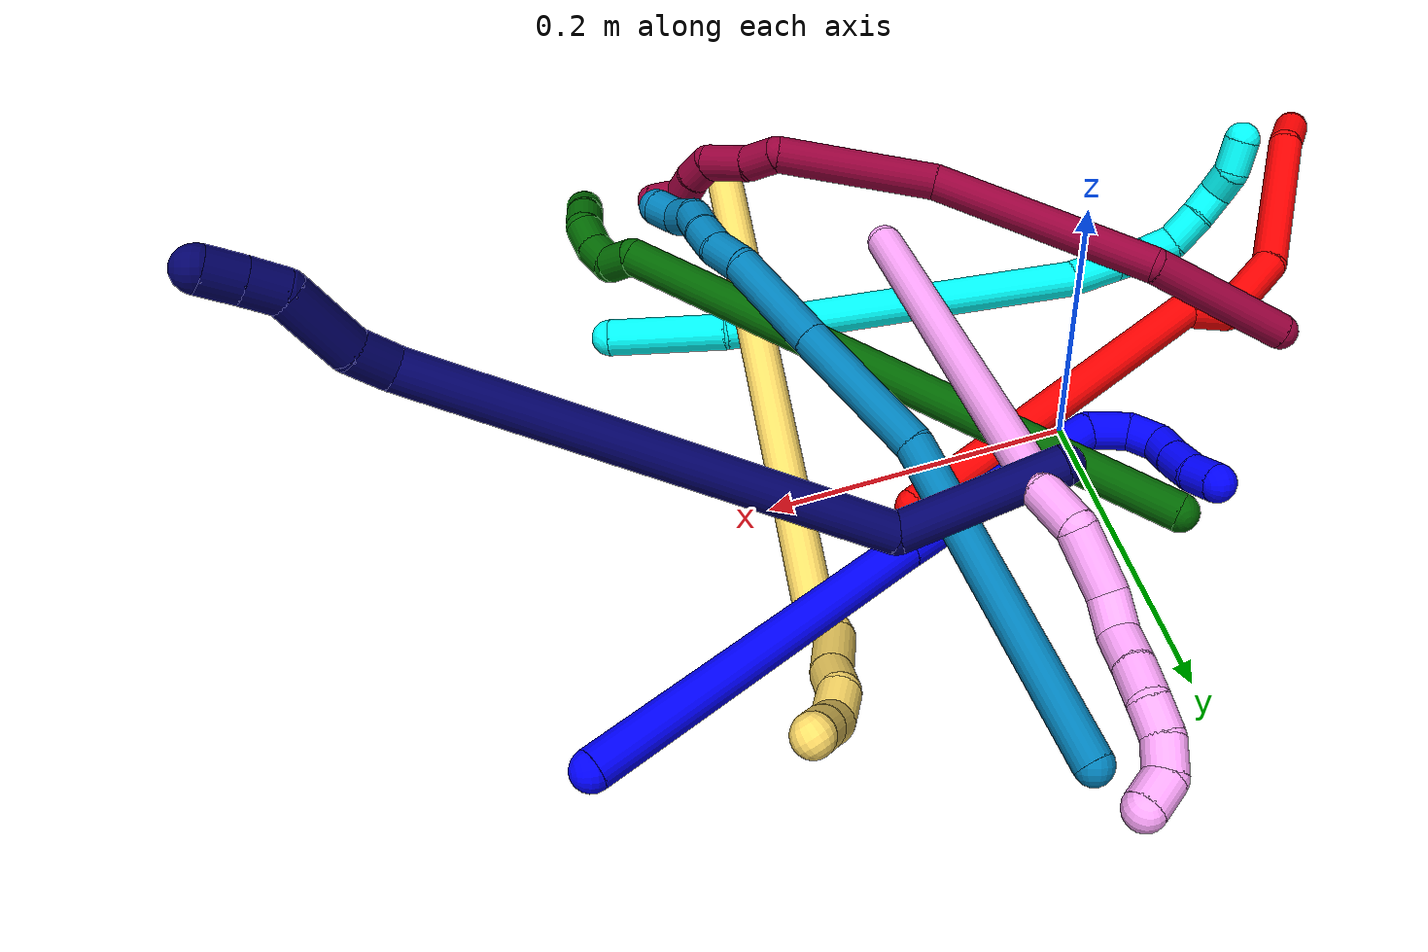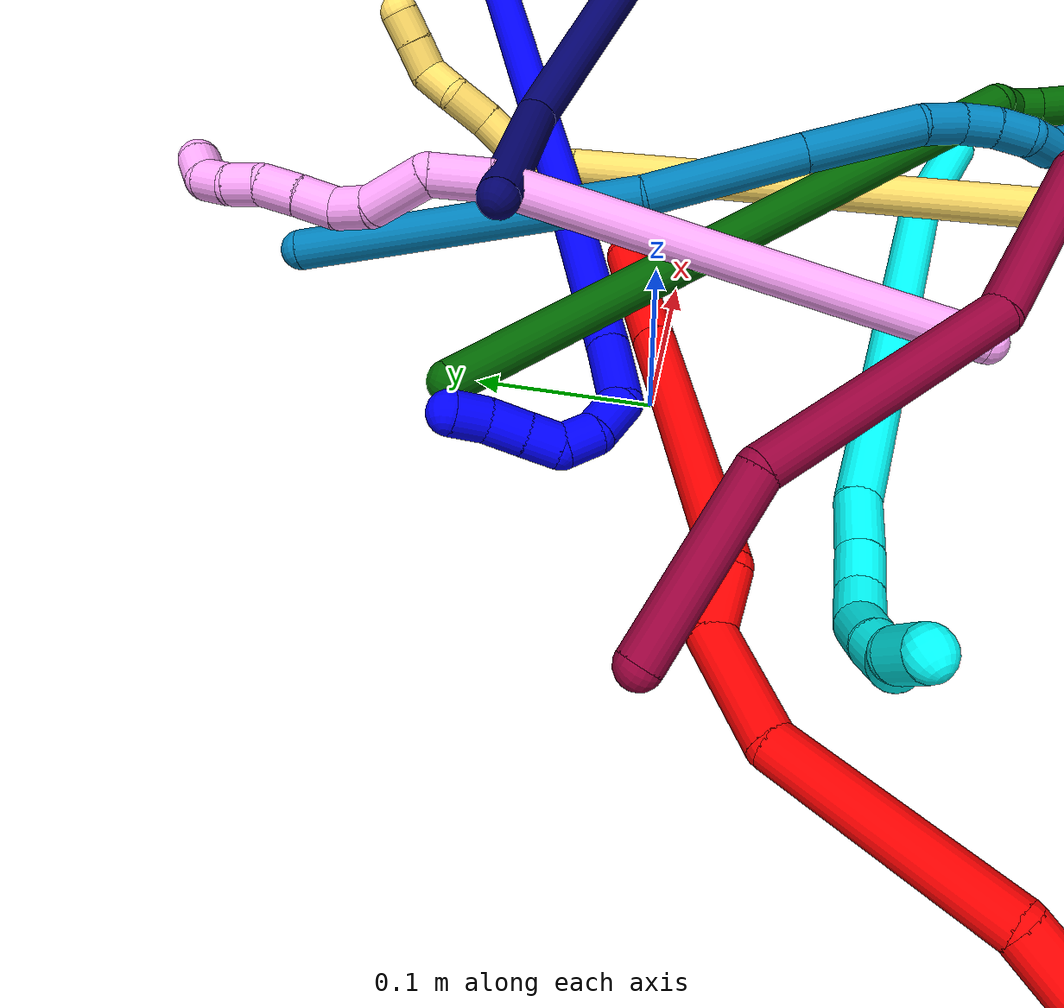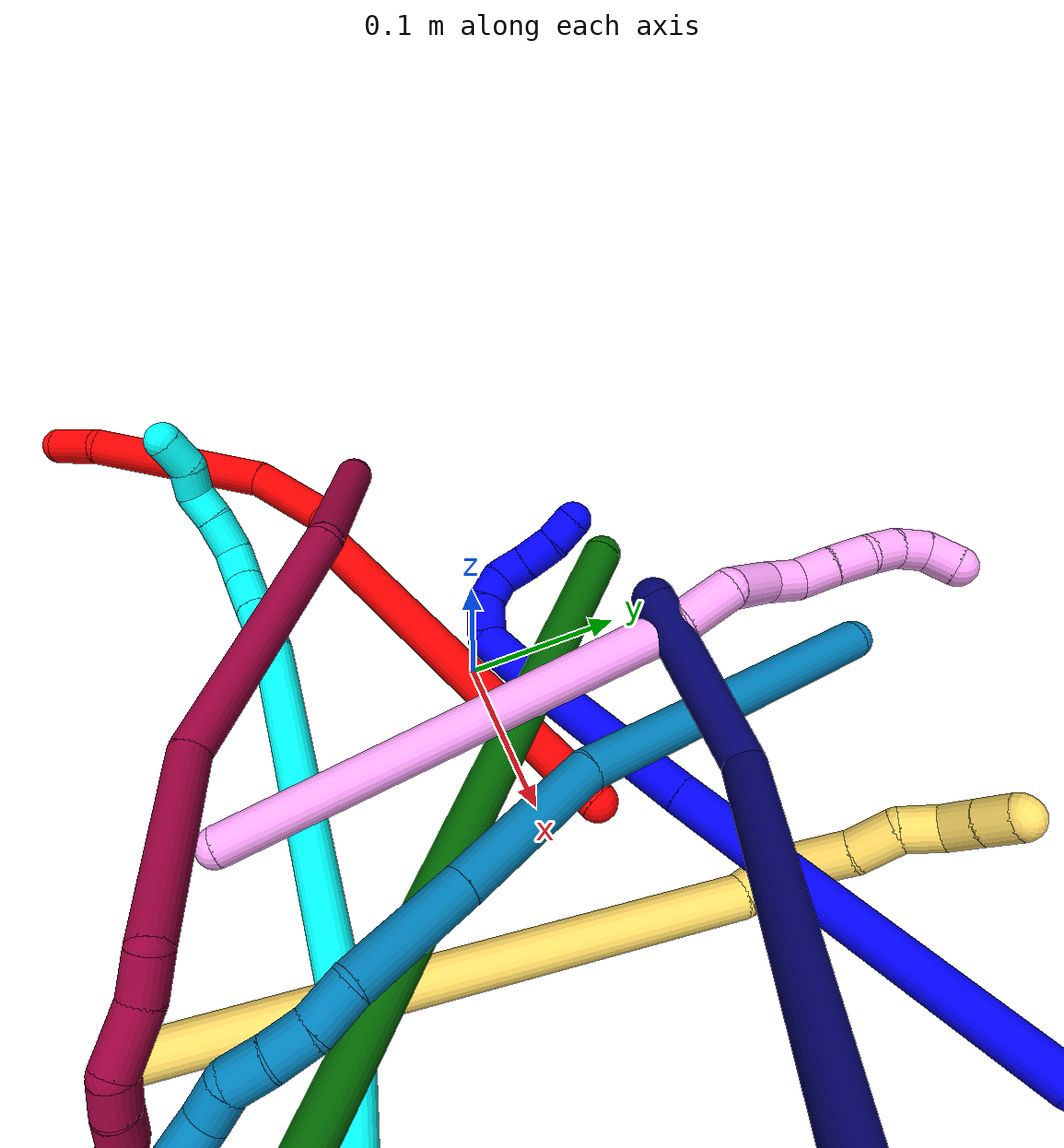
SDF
<sdf version="1.7">
 <world name="default">
  <plugin name="TubeGeneratorPlugin" filename="libtube_generator_plugin.so"/>
  <model name="photoneo_s_sensor">
   <static>1</static>
   <pose>0 0 2 1.57079 1.57079 3.14159</pose>
   <link name="link">
    <inertial><mass>0.1</mass></inertial>
    <sensor name="sensor" type="depth">
     <update_rate>30</update_rate>
     <camera>
      <horizontal_fov>1.22</horizontal_fov>
      <image><width>1920</width><height>1200</height><format>B8G8R8</format></image>
      <clip><near>0.1</near><far>4</far></clip>
      <depth_camera><output>points</output></depth_camera>
     </camera>
     <plugin name="camera_plugin" filename="libgazebo_ros_depth_camera.so">
      <baseline>0.2</baseline>
      <alwaysOn>1</alwaysOn>
      <updateRate>0.0</updateRate>
      <cameraName>camera_ir</cameraName>
      <imageTopicName>/camera/color/image_raw</imageTopicName>
      <cameraInfoTopicName>/camera/color/camera_info</cameraInfoTopicName>
      <depthImageTopicName>/camera/depth/image_raw</depthImageTopicName>
      <depthImageCameraInfoTopicName>/camera/depth/camera_info</depthImageCameraInfoTopicName>
      <pointCloudTopicName>/camera/depth/points</pointCloudTopicName>
      <frameName>fr_optical</frameName>
      <pointCloudCutoff>0.1</pointCloudCutoff>
      <pointCloudCutoffMax>2.0</pointCloudCutoffMax>
      <distortionK1>0</distortionK1>
      <distortionK2>0</distortionK2>
      <distortionK3>0</distortionK3>
      <distortionT1>0</distortionT1>
      <distortionT2>0</distortionT2>
      <CxPrime>0</CxPrime>
      <Cx>0</Cx>
      <Cy>0</Cy>
      <focalLength>0</focalLength>
      <hackBaseline>0</hackBaseline>
     </plugin>
    </sensor>
   </link>
  </model>
  <gravity>0 0 -9.8</gravity>
  <magnetic_field>6e-06 2.3e-05 -4.2e-05</magnetic_field>
  <atmosphere type="adiabatic"/>
  <physics name="default_physics" default="0" type="ode">
   <max_step_size>0.003</max_step_size>
   <real_time_factor>1</real_time_factor>
   <real_time_update_rate>1000</real_time_update_rate>
   <max_contacts>10000</max_contacts>
   <ode>
    <solver>
     <type>quick</type>
     <iters>100</iters>
     <sor>1.3</sor>
     <use_dynamic_moi_rescaling>0</use_dynamic_moi_rescaling>
    </solver>
    <constraints>
     <contact_max_correcting_vel>0</contact_max_correcting_vel>
     <contact_surface_layer>0.001</contact_surface_layer>
     <cfm>0</cfm>
     <erp>0.2</erp>
    </constraints>
   </ode>
  </physics>
  <scene><ambient>0.4 0.4 0.4 1</ambient><background>0.7 0.7 0.7 1</background><shadows>0</shadows></scene>
  <audio><device>default</device></audio>
  <spherical_coordinates>
   <surface_model>EARTH_WGS84</surface_model>
   <latitude_deg>0</latitude_deg>
   <longitude_deg>0</longitude_deg>
   <elevation>0</elevation>
   <heading_deg>0</heading_deg>
  </spherical_coordinates>
  <model name="bin">
   <static>1</static>
   <link name="bottom">
    <collision name="collision-bottom">
     <pose>0 0 -0.01 0 -0 0</pose>
     <geometry><box><size>0.8 0.6 0.02</size></box></geometry>
     <surface>
      <friction><ode><mu>100</mu><mu2>100</mu2></ode></friction>
      <contact><collide_bitmask>65535</collide_bitmask></contact>
     </surface>
    </collision>
   </link>
   <link name="west_wall">
    <collision name="collision-west_wall">
     <pose>-0.41 0 0.1 0 -0 0</pose>
     <geometry><box><size>0.02 0.6 0.2</size></box></geometry>
     <surface>
      <friction><ode><mu>100</mu><mu2>100</mu2></ode></friction>
      <contact><collide_bitmask>65535</collide_bitmask></contact>
     </surface>
    </collision>
   </link>
   <link name="east_wall">
    <collision name="collision-east_wall">
     <pose>0.41 0 0.1 0 -0 0</pose>
     <geometry><box><size>0.02 0.6 0.2</size></box></geometry>
     <surface>
      <friction><ode><mu>100</mu><mu2>100</mu2></ode></friction>
      <contact><collide_bitmask>65535</collide_bitmask></contact>
     </surface>
    </collision>
   </link>
   <link name="south_wall">
    <collision name="collision-south_wall">
     <pose>0 -0.31 0.1 0 -0 0</pose>
     <geometry><box><size>0.8 0.02 0.2</size></box></geometry>
     <surface>
      <friction><ode><mu>100</mu><mu2>100</mu2></ode></friction>
      <contact><collide_bitmask>65535</collide_bitmask></contact>
     </surface>
    </collision>
   </link>
   <link name="north_wall">
    <collision name="collision-north_wall">
     <pose>0 0.31 0.1 0 -0 0</pose>
     <geometry><box><size>0.8 0.02 0.2</size></box></geometry>
     <surface>
      <friction><ode><mu>100</mu><mu2>100</mu2></ode></friction>
      <contact><collide_bitmask>65535</collide_bitmask></contact>
     </surface>
    </collision>
   </link>
  </model>
  <model name="1">
   <static>0</static>
   <link name="1">
    <collision name="collision-cylinder-e_1_1_4">
     <pose>-0.006613 -0.04059 -0.106504 2.77748 -0.057953 -0.312323</pose>
     <geometry><cylinder><radius>0.0125</radius><length>0.228337</length></cylinder></geometry>
     <surface>
      <friction><ode><mu>1.16</mu><mu2>1.16</mu2><slip1>0</slip1><slip2>0</slip2></ode></friction>
      <contact><ode><kp>1e+06</kp><kd>1</kd><max_vel>0</max_vel><min_depth>0.001</min_depth></ode></contact>
     </surface>
    </collision>
    <visual name="visual-cylinder-e_1_1_4">
     <pose>-0.006613 -0.04059 -0.106504 2.77748 -0.057953 -0.312323</pose>
     <geometry><cylinder><radius>0.0125</radius><length>0.228337</length></cylinder></geometry>
     <material><ambient>0 0 1 1</ambient></material>
    </visual>
    <collision name="collision-cylinder-e_2_4_5">
     <pose>-0.016884 -0.101074 -0.269164 2.80113 -0.061324 -0.353146</pose>
     <geometry><cylinder><radius>0.0125</radius><length>0.119375</length></cylinder></geometry>
     <surface>
      <friction><ode><mu>1.16</mu><mu2>1.16</mu2><slip1>0</slip1><slip2>0</slip2></ode></friction>
      <contact><ode><kp>1e+06</kp><kd>1</kd><max_vel>0</max_vel><min_depth>0.001</min_depth></ode></contact>
     </surface>
    </collision>
    <visual name="visual-cylinder-e_2_4_5">
     <pose>-0.016884 -0.101074 -0.269164 2.80113 -0.061324 -0.353146</pose>
     <geometry><cylinder><radius>0.0125</radius><length>0.119375</length></cylinder></geometry>
     <material><ambient>0 0 1 1</ambient></material>
    </visual>
    <collision name="collision-cylinder-e_3_5_6">
     <pose>-0.022956 -0.127219 -0.344684 2.82931 -0.11809 -0.718445</pose>
     <geometry><cylinder><radius>0.0125</radius><length>0.040981</length></cylinder></geometry>
     <surface>
      <friction><ode><mu>1.16</mu><mu2>1.16</mu2><slip1>0</slip1><slip2>0</slip2></ode></friction>
      <contact><ode><kp>1e+06</kp><kd>1</kd><max_vel>0</max_vel><min_depth>0.001</min_depth></ode></contact>
     </surface>
    </collision>
    <visual name="visual-cylinder-e_3_5_6">
     <pose>-0.022956 -0.127219 -0.344684 2.82931 -0.11809 -0.718445</pose>
     <geometry><cylinder><radius>0.0125</radius><length>0.040981</length></cylinder></geometry>
     <material><ambient>0 0 1 1</ambient></material>
    </visual>
    <collision name="collision-cylinder-e_4_6_7">
     <pose>-0.030035 -0.12842 -0.375773 -2.73487 -0.350362 1.4186</pose>
     <geometry><cylinder><radius>0.0125</radius><length>0.027186</length></cylinder></geometry>
     <surface>
      <friction><ode><mu>1.16</mu><mu2>1.16</mu2><slip1>0</slip1><slip2>0</slip2></ode></friction>
      <contact><ode><kp>1e+06</kp><kd>1</kd><max_vel>0</max_vel><min_depth>0.001</min_depth></ode></contact>
     </surface>
    </collision>
    <visual name="visual-cylinder-e_4_6_7">
     <pose>-0.030035 -0.12842 -0.375773 -2.73487 -0.350362 1.4186</pose>
     <geometry><cylinder><radius>0.0125</radius><length>0.027186</length></cylinder></geometry>
     <material><ambient>0 0 1 1</ambient></material>
    </visual>
    <collision name="collision-cylinder-e_5_7_8">
     <pose>-0.038416 -0.115654 -0.393464 -2.22902 -0.363999 0.717449</pose>
     <geometry><cylinder><radius>0.0125</radius><length>0.020872</length></cylinder></geometry>
     <surface>
      <friction><ode><mu>1.16</mu><mu2>1.16</mu2><slip1>0</slip1><slip2>0</slip2></ode></friction>
      <contact><ode><kp>1e+06</kp><kd>1</kd><max_vel>0</max_vel><min_depth>0.001</min_depth></ode></contact>
     </surface>
    </collision>
    <visual name="visual-cylinder-e_5_7_8">
     <pose>-0.038416 -0.115654 -0.393464 -2.22902 -0.363999 0.717449</pose>
     <geometry><cylinder><radius>0.0125</radius><length>0.020872</length></cylinder></geometry>
     <material><ambient>0 0 1 1</ambient></material>
    </visual>
    <collision name="collision-cylinder-e_6_8_9">
     <pose>-0.047348 -0.099367 -0.398174 -1.42532 -0.541912 0.47119</pose>
     <geometry><cylinder><radius>0.0125</radius><length>0.020225</length></cylinder></geometry>
     <surface>
      <friction><ode><mu>1.16</mu><mu2>1.16</mu2><slip1>0</slip1><slip2>0</slip2></ode></friction>
      <contact><ode><kp>1e+06</kp><kd>1</kd><max_vel>0</max_vel><min_depth>0.001</min_depth></ode></contact>
     </surface>
    </collision>
    <visual name="visual-cylinder-e_6_8_9">
     <pose>-0.047348 -0.099367 -0.398174 -1.42532 -0.541912 0.47119</pose>
     <geometry><cylinder><radius>0.0125</radius><length>0.020225</length></cylinder></geometry>
     <material><ambient>0 0 1 1</ambient></material>
    </visual>
    <collision name="collision-cylinder-e_7_9_10">
     <pose>-0.05922 -0.081665 -0.395887 -1.45833 -0.62697 0.563821</pose>
     <geometry><cylinder><radius>0.0125</radius><length>0.022691</length></cylinder></geometry>
     <surface>
      <friction><ode><mu>1.16</mu><mu2>1.16</mu2><slip1>0</slip1><slip2>0</slip2></ode></friction>
      <contact><ode><kp>1e+06</kp><kd>1</kd><max_vel>0</max_vel><min_depth>0.001</min_depth></ode></contact>
     </surface>
    </collision>
    <visual name="visual-cylinder-e_7_9_10">
     <pose>-0.05922 -0.081665 -0.395887 -1.45833 -0.62697 0.563821</pose>
     <geometry><cylinder><radius>0.0125</radius><length>0.022691</length></cylinder></geometry>
     <material><ambient>0 0 1 1</ambient></material>
    </visual>
    <collision name="collision-cylinder-e_8_10_2">
     <pose>-0.072529 -0.064958 -0.396149 -1.73979 -0.713363 0.831662</pose>
     <geometry><cylinder><radius>0.0125</radius><length>0.020333</length></cylinder></geometry>
     <surface>
      <friction><ode><mu>1.16</mu><mu2>1.16</mu2><slip1>0</slip1><slip2>0</slip2></ode></friction>
      <contact><ode><kp>1e+06</kp><kd>1</kd><max_vel>0</max_vel><min_depth>0.001</min_depth></ode></contact>
     </surface>
    </collision>
    <visual name="visual-cylinder-e_8_10_2">
     <pose>-0.072529 -0.064958 -0.396149 -1.73979 -0.713363 0.831662</pose>
     <geometry><cylinder><radius>0.0125</radius><length>0.020333</length></cylinder></geometry>
     <material><ambient>0 0 1 1</ambient></material>
    </visual>
    <collision name="collision-sphere-2">
     <pose>-0.079181 -0.05738 -0.397442 0 -0 0</pose>
     <geometry><sphere><radius>0.0125</radius></sphere></geometry>
     <surface>
      <friction><ode><mu>1.16</mu><mu2>1.16</mu2><slip1>0</slip1><slip2>0</slip2></ode></friction>
      <contact><ode><kp>1e+06</kp><kd>1</kd><max_vel>0</max_vel><min_depth>0.001</min_depth></ode></contact>
     </surface>
    </collision>
    <visual name="visual-sphere-2">
     <pose>-0.079181 -0.05738 -0.397442 0 -0 0</pose>
     <geometry><sphere><radius>0.0125</radius></sphere></geometry>
     <material><ambient>0 0 1 1</ambient></material>
    </visual>
    <collision name="collision-sphere-10">
     <pose>-0.065876 -0.072535 -0.394856 0 -0 0</pose>
     <geometry><sphere><radius>0.0125</radius></sphere></geometry>
     <surface>
      <friction><ode><mu>1.16</mu><mu2>1.16</mu2><slip1>0</slip1><slip2>0</slip2></ode></friction>
      <contact><ode><kp>1e+06</kp><kd>1</kd><max_vel>0</max_vel><min_depth>0.001</min_depth></ode></contact>
     </surface>
    </collision>
    <visual name="visual-sphere-10">
     <pose>-0.065876 -0.072535 -0.394856 0 -0 0</pose>
     <geometry><sphere><radius>0.0125</radius></sphere></geometry>
     <material><ambient>0 0 1 1</ambient></material>
    </visual>
    <collision name="collision-sphere-9">
     <pose>-0.052563 -0.090795 -0.396918 0 -0 0</pose>
     <geometry><sphere><radius>0.0125</radius></sphere></geometry>
     <surface>
      <friction><ode><mu>1.16</mu><mu2>1.16</mu2><slip1>0</slip1><slip2>0</slip2></ode></friction>
      <contact><ode><kp>1e+06</kp><kd>1</kd><max_vel>0</max_vel><min_depth>0.001</min_depth></ode></contact>
     </surface>
    </collision>
    <visual name="visual-sphere-9">
     <pose>-0.052563 -0.090795 -0.396918 0 -0 0</pose>
     <geometry><sphere><radius>0.0125</radius></sphere></geometry>
     <material><ambient>0 0 1 1</ambient></material>
    </visual>
    <collision name="collision-sphere-4">
     <pose>-0.013226 -0.08118 -0.213009 0 -0 0</pose>
     <geometry><sphere><radius>0.0125</radius></sphere></geometry>
     <surface>
      <friction><ode><mu>1.16</mu><mu2>1.16</mu2><slip1>0</slip1><slip2>0</slip2></ode></friction>
      <contact><ode><kp>1e+06</kp><kd>1</kd><max_vel>0</max_vel><min_depth>0.001</min_depth></ode></contact>
     </surface>
    </collision>
    <visual name="visual-sphere-4">
     <pose>-0.013226 -0.08118 -0.213009 0 -0 0</pose>
     <geometry><sphere><radius>0.0125</radius></sphere></geometry>
     <material><ambient>0 0 1 1</ambient></material>
    </visual>
    <collision name="collision-sphere-1">
     <geometry><sphere><radius>0.0125</radius></sphere></geometry>
     <surface>
      <friction><ode><mu>1.16</mu><mu2>1.16</mu2><slip1>0</slip1><slip2>0</slip2></ode></friction>
      <contact><ode><kp>1e+06</kp><kd>1</kd><max_vel>0</max_vel><min_depth>0.001</min_depth></ode></contact>
     </surface>
    </collision>
    <visual name="visual-sphere-1">
     <geometry><sphere><radius>0.0125</radius></sphere></geometry>
     <material><ambient>0 0 1 1</ambient></material>
    </visual>
    <collision name="collision-sphere-8">
     <pose>-0.042132 -0.107939 -0.39943 0 -0 0</pose>
     <geometry><sphere><radius>0.0125</radius></sphere></geometry>
     <surface>
      <friction><ode><mu>1.16</mu><mu2>1.16</mu2><slip1>0</slip1><slip2>0</slip2></ode></friction>
      <contact><ode><kp>1e+06</kp><kd>1</kd><max_vel>0</max_vel><min_depth>0.001</min_depth></ode></contact>
     </surface>
    </collision>
    <visual name="visual-sphere-8">
     <pose>-0.042132 -0.107939 -0.39943 0 -0 0</pose>
     <geometry><sphere><radius>0.0125</radius></sphere></geometry>
     <material><ambient>0 0 1 1</ambient></material>
    </visual>
    <collision name="collision-sphere-5">
     <pose>-0.020542 -0.120968 -0.32532 0 -0 0</pose>
     <geometry><sphere><radius>0.0125</radius></sphere></geometry>
     <surface>
      <friction><ode><mu>1.16</mu><mu2>1.16</mu2><slip1>0</slip1><slip2>0</slip2></ode></friction>
      <contact><ode><kp>1e+06</kp><kd>1</kd><max_vel>0</max_vel><min_depth>0.001</min_depth></ode></contact>
     </surface>
    </collision>
    <visual name="visual-sphere-5">
     <pose>-0.020542 -0.120968 -0.32532 0 -0 0</pose>
     <geometry><sphere><radius>0.0125</radius></sphere></geometry>
     <material><ambient>0 0 1 1</ambient></material>
    </visual>
    <collision name="collision-sphere-6">
     <pose>-0.02537 -0.13347 -0.364047 0 -0 0</pose>
     <geometry><sphere><radius>0.0125</radius></sphere></geometry>
     <surface>
      <friction><ode><mu>1.16</mu><mu2>1.16</mu2><slip1>0</slip1><slip2>0</slip2></ode></friction>
      <contact><ode><kp>1e+06</kp><kd>1</kd><max_vel>0</max_vel><min_depth>0.001</min_depth></ode></contact>
     </surface>
    </collision>
    <visual name="visual-sphere-6">
     <pose>-0.02537 -0.13347 -0.364047 0 -0 0</pose>
     <geometry><sphere><radius>0.0125</radius></sphere></geometry>
     <material><ambient>0 0 1 1</ambient></material>
    </visual>
    <collision name="collision-sphere-7">
     <pose>-0.034701 -0.123369 -0.387499 0 -0 0</pose>
     <geometry><sphere><radius>0.0125</radius></sphere></geometry>
     <surface>
      <friction><ode><mu>1.16</mu><mu2>1.16</mu2><slip1>0</slip1><slip2>0</slip2></ode></friction>
      <contact><ode><kp>1e+06</kp><kd>1</kd><max_vel>0</max_vel><min_depth>0.001</min_depth></ode></contact>
     </surface>
    </collision>
    <visual name="visual-sphere-7">
     <pose>-0.034701 -0.123369 -0.387499 0 -0 0</pose>
     <geometry><sphere><radius>0.0125</radius></sphere></geometry>
     <material><ambient>0 0 1 1</ambient></material>
    </visual>
    <inertial>
     <pose>-0.019721 -0.075272 -0.22819 0 -0 0</pose>
     <mass>0.5</mass>
     <inertia>
      <ixx>0.000735</ixx>
      <ixy>0</ixy>
      <ixz>0</ixz>
      <iyy>-0.001377</iyy>
      <iyz>0</iyz>
      <izz>0.000442</izz>
     </inertia>
    </inertial>
   </link>
   <pose>0.341375 0.169291 0.055638 -0.672979 1.23132 -0.619052</pose>
  </model>
  <model name="2">
   <static>0</static>
   <link name="2">
    <collision name="collision-cylinder-e_1_1_4">
     <pose>-0.034632 -0.018535 0.011125 1.03022 -1.01277 -0.608442</pose>
     <geometry><cylinder><radius>0.0125</radius><length>0.08165</length></cylinder></geometry>
     <surface>
      <friction><ode><mu>1.16</mu><mu2>1.16</mu2><slip1>0</slip1><slip2>0</slip2></ode></friction>
      <contact><ode><kp>1e+06</kp><kd>1</kd><max_vel>0</max_vel><min_depth>0.001</min_depth></ode></contact>
     </surface>
    </collision>
    <visual name="visual-cylinder-e_1_1_4">
     <pose>-0.034632 -0.018535 0.011125 1.03022 -1.01277 -0.608442</pose>
     <geometry><cylinder><radius>0.0125</radius><length>0.08165</length></cylinder></geometry>
     <material><ambient>1 0 0 1</ambient></material>
    </visual>
    <collision name="collision-cylinder-e_2_4_5">
     <pose>-0.139704 -0.075098 0.044889 1.03381 -1.00983 -0.608848</pose>
     <geometry><cylinder><radius>0.0125</radius><length>0.166379</length></cylinder></geometry>
     <surface>
      <friction><ode><mu>1.16</mu><mu2>1.16</mu2><slip1>0</slip1><slip2>0</slip2></ode></friction>
      <contact><ode><kp>1e+06</kp><kd>1</kd><max_vel>0</max_vel><min_depth>0.001</min_depth></ode></contact>
     </surface>
    </collision>
    <visual name="visual-cylinder-e_2_4_5">
     <pose>-0.139704 -0.075098 0.044889 1.03381 -1.00983 -0.608848</pose>
     <geometry><cylinder><radius>0.0125</radius><length>0.166379</length></cylinder></geometry>
     <material><ambient>1 0 0 1</ambient></material>
    </visual>
    <collision name="collision-cylinder-e_3_5_6">
     <pose>-0.226825 -0.113369 0.065898 2.99337 -1.4723 -2.97806</pose>
     <geometry><cylinder><radius>0.0125</radius><length>0.033523</length></cylinder></geometry>
     <surface>
      <friction><ode><mu>1.16</mu><mu2>1.16</mu2><slip1>0</slip1><slip2>0</slip2></ode></friction>
      <contact><ode><kp>1e+06</kp><kd>1</kd><max_vel>0</max_vel><min_depth>0.001</min_depth></ode></contact>
     </surface>
    </collision>
    <visual name="visual-cylinder-e_3_5_6">
     <pose>-0.226825 -0.113369 0.065898 2.99337 -1.4723 -2.97806</pose>
     <geometry><cylinder><radius>0.0125</radius><length>0.033523</length></cylinder></geometry>
     <material><ambient>1 0 0 1</ambient></material>
    </visual>
    <collision name="collision-cylinder-e_4_6_7">
     <pose>-0.266298 -0.132873 0.070943 1.23718 -0.841128 -0.616399</pose>
     <geometry><cylinder><radius>0.0125</radius><length>0.061156</length></cylinder></geometry>
     <surface>
      <friction><ode><mu>1.16</mu><mu2>1.16</mu2><slip1>0</slip1><slip2>0</slip2></ode></friction>
      <contact><ode><kp>1e+06</kp><kd>1</kd><max_vel>0</max_vel><min_depth>0.001</min_depth></ode></contact>
     </surface>
    </collision>
    <visual name="visual-cylinder-e_4_6_7">
     <pose>-0.266298 -0.132873 0.070943 1.23718 -0.841128 -0.616399</pose>
     <geometry><cylinder><radius>0.0125</radius><length>0.061156</length></cylinder></geometry>
     <material><ambient>1 0 0 1</ambient></material>
    </visual>
    <collision name="collision-cylinder-e_5_7_8">
     <pose>-0.313047 -0.205436 0.093455 1.28199 -0.406792 -0.305365</pose>
     <geometry><cylinder><radius>0.0125</radius><length>0.121093</length></cylinder></geometry>
     <surface>
      <friction><ode><mu>1.16</mu><mu2>1.16</mu2><slip1>0</slip1><slip2>0</slip2></ode></friction>
      <contact><ode><kp>1e+06</kp><kd>1</kd><max_vel>0</max_vel><min_depth>0.001</min_depth></ode></contact>
     </surface>
    </collision>
    <visual name="visual-cylinder-e_5_7_8">
     <pose>-0.313047 -0.205436 0.093455 1.28199 -0.406792 -0.305365</pose>
     <geometry><cylinder><radius>0.0125</radius><length>0.121093</length></cylinder></geometry>
     <material><ambient>1 0 0 1</ambient></material>
    </visual>
    <collision name="collision-cylinder-e_6_8_2">
     <pose>-0.346994 -0.273701 0.107325 1.70148 -0.584804 -0.661183</pose>
     <geometry><cylinder><radius>0.0125</radius><length>0.036199</length></cylinder></geometry>
     <surface>
      <friction><ode><mu>1.16</mu><mu2>1.16</mu2><slip1>0</slip1><slip2>0</slip2></ode></friction>
      <contact><ode><kp>1e+06</kp><kd>1</kd><max_vel>0</max_vel><min_depth>0.001</min_depth></ode></contact>
     </surface>
    </collision>
    <visual name="visual-cylinder-e_6_8_2">
     <pose>-0.346994 -0.273701 0.107325 1.70148 -0.584804 -0.661183</pose>
     <geometry><cylinder><radius>0.0125</radius><length>0.036199</length></cylinder></geometry>
     <material><ambient>1 0 0 1</ambient></material>
    </visual>
    <collision name="collision-sphere-2">
     <pose>-0.356986 -0.288664 0.105359 0 -0 0</pose>
     <geometry><sphere><radius>0.0125</radius></sphere></geometry>
     <surface>
      <friction><ode><mu>1.16</mu><mu2>1.16</mu2><slip1>0</slip1><slip2>0</slip2></ode></friction>
      <contact><ode><kp>1e+06</kp><kd>1</kd><max_vel>0</max_vel><min_depth>0.001</min_depth></ode></contact>
     </surface>
    </collision>
    <visual name="visual-sphere-2">
     <pose>-0.356986 -0.288664 0.105359 0 -0 0</pose>
     <geometry><sphere><radius>0.0125</radius></sphere></geometry>
     <material><ambient>1 0 0 1</ambient></material>
    </visual>
    <collision name="collision-sphere-4">
     <pose>-0.069264 -0.03707 0.02225 0 -0 0</pose>
     <geometry><sphere><radius>0.0125</radius></sphere></geometry>
     <surface>
      <friction><ode><mu>1.16</mu><mu2>1.16</mu2><slip1>0</slip1><slip2>0</slip2></ode></friction>
      <contact><ode><kp>1e+06</kp><kd>1</kd><max_vel>0</max_vel><min_depth>0.001</min_depth></ode></contact>
     </surface>
    </collision>
    <visual name="visual-sphere-4">
     <pose>-0.069264 -0.03707 0.02225 0 -0 0</pose>
     <geometry><sphere><radius>0.0125</radius></sphere></geometry>
     <material><ambient>1 0 0 1</ambient></material>
    </visual>
    <collision name="collision-sphere-1">
     <geometry><sphere><radius>0.0125</radius></sphere></geometry>
     <surface>
      <friction><ode><mu>1.16</mu><mu2>1.16</mu2><slip1>0</slip1><slip2>0</slip2></ode></friction>
      <contact><ode><kp>1e+06</kp><kd>1</kd><max_vel>0</max_vel><min_depth>0.001</min_depth></ode></contact>
     </surface>
    </collision>
    <visual name="visual-sphere-1">
     <geometry><sphere><radius>0.0125</radius></sphere></geometry>
     <material><ambient>1 0 0 1</ambient></material>
    </visual>
    <collision name="collision-sphere-8">
     <pose>-0.337003 -0.258738 0.109292 0 -0 0</pose>
     <geometry><sphere><radius>0.0125</radius></sphere></geometry>
     <surface>
      <friction><ode><mu>1.16</mu><mu2>1.16</mu2><slip1>0</slip1><slip2>0</slip2></ode></friction>
      <contact><ode><kp>1e+06</kp><kd>1</kd><max_vel>0</max_vel><min_depth>0.001</min_depth></ode></contact>
     </surface>
    </collision>
    <visual name="visual-sphere-8">
     <pose>-0.337003 -0.258738 0.109292 0 -0 0</pose>
     <geometry><sphere><radius>0.0125</radius></sphere></geometry>
     <material><ambient>1 0 0 1</ambient></material>
    </visual>
    <collision name="collision-sphere-5">
     <pose>-0.210144 -0.113126 0.067529 0 -0 0</pose>
     <geometry><sphere><radius>0.0125</radius></sphere></geometry>
     <surface>
      <friction><ode><mu>1.16</mu><mu2>1.16</mu2><slip1>0</slip1><slip2>0</slip2></ode></friction>
      <contact><ode><kp>1e+06</kp><kd>1</kd><max_vel>0</max_vel><min_depth>0.001</min_depth></ode></contact>
     </surface>
    </collision>
    <visual name="visual-sphere-5">
     <pose>-0.210144 -0.113126 0.067529 0 -0 0</pose>
     <geometry><sphere><radius>0.0125</radius></sphere></geometry>
     <material><ambient>1 0 0 1</ambient></material>
    </visual>
    <collision name="collision-sphere-6">
     <pose>-0.243505 -0.113613 0.064268 0 -0 0</pose>
     <geometry><sphere><radius>0.0125</radius></sphere></geometry>
     <surface>
      <friction><ode><mu>1.16</mu><mu2>1.16</mu2><slip1>0</slip1><slip2>0</slip2></ode></friction>
      <contact><ode><kp>1e+06</kp><kd>1</kd><max_vel>0</max_vel><min_depth>0.001</min_depth></ode></contact>
     </surface>
    </collision>
    <visual name="visual-sphere-6">
     <pose>-0.243505 -0.113613 0.064268 0 -0 0</pose>
     <geometry><sphere><radius>0.0125</radius></sphere></geometry>
     <material><ambient>1 0 0 1</ambient></material>
    </visual>
    <collision name="collision-sphere-7">
     <pose>-0.28909 -0.152133 0.077618 0 -0 0</pose>
     <geometry><sphere><radius>0.0125</radius></sphere></geometry>
     <surface>
      <friction><ode><mu>1.16</mu><mu2>1.16</mu2><slip1>0</slip1><slip2>0</slip2></ode></friction>
      <contact><ode><kp>1e+06</kp><kd>1</kd><max_vel>0</max_vel><min_depth>0.001</min_depth></ode></contact>
     </surface>
    </collision>
    <visual name="visual-sphere-7">
     <pose>-0.28909 -0.152133 0.077618 0 -0 0</pose>
     <geometry><sphere><radius>0.0125</radius></sphere></geometry>
     <material><ambient>1 0 0 1</ambient></material>
    </visual>
    <inertial>
     <pose>-0.200859 -0.121438 0.060253 0 -0 0</pose>
     <mass>0.5</mass>
     <inertia>
      <ixx>0.000125</ixx>
      <ixy>0</ixy>
      <ixz>0</ixz>
      <iyy>0.000237</iyy>
      <iyz>0</iyz>
      <izz>0.000817</izz>
     </inertia>
    </inertial>
   </link>
   <pose>0.114167 0.03373 0.009665 0.092354 -0.217867 -0.127751</pose>
  </model>
  <model name="3">
   <static>0</static>
   <link name="3">
    <collision name="collision-cylinder-e_1_1_4">
     <pose>-0.027991 -0.014744 0.024667 0.538759 -0.772234 -0.223539</pose>
     <geometry><cylinder><radius>0.0125</radius><length>0.080233</length></cylinder></geometry>
     <surface>
      <friction><ode><mu>1.16</mu><mu2>1.16</mu2><slip1>0</slip1><slip2>0</slip2></ode></friction>
      <contact><ode><kp>1e+06</kp><kd>1</kd><max_vel>0</max_vel><min_depth>0.001</min_depth></ode></contact>
     </surface>
    </collision>
    <visual name="visual-cylinder-e_1_1_4">
     <pose>-0.027991 -0.014744 0.024667 0.538759 -0.772234 -0.223539</pose>
     <geometry><cylinder><radius>0.0125</radius><length>0.080233</length></cylinder></geometry>
     <material><ambient>0.003922 1 0.996078 1</ambient></material>
    </visual>
    <collision name="collision-cylinder-e_2_4_5">
     <pose>-0.12638 -0.070525 0.143132 0.4124 -0.60236 -0.129768</pose>
     <geometry><cylinder><radius>0.0125</radius><length>0.2485</length></cylinder></geometry>
     <surface>
      <friction><ode><mu>1.16</mu><mu2>1.16</mu2><slip1>0</slip1><slip2>0</slip2></ode></friction>
      <contact><ode><kp>1e+06</kp><kd>1</kd><max_vel>0</max_vel><min_depth>0.001</min_depth></ode></contact>
     </surface>
    </collision>
    <visual name="visual-cylinder-e_2_4_5">
     <pose>-0.12638 -0.070525 0.143132 0.4124 -0.60236 -0.129768</pose>
     <geometry><cylinder><radius>0.0125</radius><length>0.2485</length></cylinder></geometry>
     <material><ambient>0.003922 1 0.996078 1</ambient></material>
    </visual>
    <collision name="collision-cylinder-e_3_5_6">
     <pose>-0.204993 -0.114925 0.251573 0.225878 -0.500317 -0.057945</pose>
     <geometry><cylinder><radius>0.0125</radius><length>0.034245</length></cylinder></geometry>
     <surface>
      <friction><ode><mu>1.16</mu><mu2>1.16</mu2><slip1>0</slip1><slip2>0</slip2></ode></friction>
      <contact><ode><kp>1e+06</kp><kd>1</kd><max_vel>0</max_vel><min_depth>0.001</min_depth></ode></contact>
     </surface>
    </collision>
    <visual name="visual-cylinder-e_3_5_6">
     <pose>-0.204993 -0.114925 0.251573 0.225878 -0.500317 -0.057945</pose>
     <geometry><cylinder><radius>0.0125</radius><length>0.034245</length></cylinder></geometry>
     <material><ambient>0.003922 1 0.996078 1</ambient></material>
    </visual>
    <collision name="collision-cylinder-e_4_6_7">
     <pose>-0.219396 -0.120826 0.276358 0.245019 -0.534486 -0.067396</pose>
     <geometry><cylinder><radius>0.0125</radius><length>0.0243</length></cylinder></geometry>
     <surface>
      <friction><ode><mu>1.16</mu><mu2>1.16</mu2><slip1>0</slip1><slip2>0</slip2></ode></friction>
      <contact><ode><kp>1e+06</kp><kd>1</kd><max_vel>0</max_vel><min_depth>0.001</min_depth></ode></contact>
     </surface>
    </collision>
    <visual name="visual-cylinder-e_4_6_7">
     <pose>-0.219396 -0.120826 0.276358 0.245019 -0.534486 -0.067396</pose>
     <geometry><cylinder><radius>0.0125</radius><length>0.0243</length></cylinder></geometry>
     <material><ambient>0.003922 1 0.996078 1</ambient></material>
    </visual>
    <collision name="collision-cylinder-e_5_7_8">
     <pose>-0.232432 -0.123976 0.295166 0.070738 -0.667558 -0.024538</pose>
     <geometry><cylinder><radius>0.0125</radius><length>0.022119</length></cylinder></geometry>
     <surface>
      <friction><ode><mu>1.16</mu><mu2>1.16</mu2><slip1>0</slip1><slip2>0</slip2></ode></friction>
      <contact><ode><kp>1e+06</kp><kd>1</kd><max_vel>0</max_vel><min_depth>0.001</min_depth></ode></contact>
     </surface>
    </collision>
    <visual name="visual-cylinder-e_5_7_8">
     <pose>-0.232432 -0.123976 0.295166 0.070738 -0.667558 -0.024538</pose>
     <geometry><cylinder><radius>0.0125</radius><length>0.022119</length></cylinder></geometry>
     <material><ambient>0.003922 1 0.996078 1</ambient></material>
    </visual>
    <collision name="collision-cylinder-e_6_8_9">
     <pose>-0.247185 -0.119418 0.312746 -0.525637 -0.654329 0.182099</pose>
     <geometry><cylinder><radius>0.0125</radius><length>0.025982</length></cylinder></geometry>
     <surface>
      <friction><ode><mu>1.16</mu><mu2>1.16</mu2><slip1>0</slip1><slip2>0</slip2></ode></friction>
      <contact><ode><kp>1e+06</kp><kd>1</kd><max_vel>0</max_vel><min_depth>0.001</min_depth></ode></contact>
     </surface>
    </collision>
    <visual name="visual-cylinder-e_6_8_9">
     <pose>-0.247185 -0.119418 0.312746 -0.525637 -0.654329 0.182099</pose>
     <geometry><cylinder><radius>0.0125</radius><length>0.025982</length></cylinder></geometry>
     <material><ambient>0.003922 1 0.996078 1</ambient></material>
    </visual>
    <collision name="collision-cylinder-e_7_9_10">
     <pose>-0.260072 -0.109942 0.3296 -0.496836 -0.50406 0.130451</pose>
     <geometry><cylinder><radius>0.0125</radius><length>0.020624</length></cylinder></geometry>
     <surface>
      <friction><ode><mu>1.16</mu><mu2>1.16</mu2><slip1>0</slip1><slip2>0</slip2></ode></friction>
      <contact><ode><kp>1e+06</kp><kd>1</kd><max_vel>0</max_vel><min_depth>0.001</min_depth></ode></contact>
     </surface>
    </collision>
    <visual name="visual-cylinder-e_7_9_10">
     <pose>-0.260072 -0.109942 0.3296 -0.496836 -0.50406 0.130451</pose>
     <geometry><cylinder><radius>0.0125</radius><length>0.020624</length></cylinder></geometry>
     <material><ambient>0.003922 1 0.996078 1</ambient></material>
    </visual>
    <collision name="collision-cylinder-e_8_10_11">
     <pose>-0.273004 -0.099441 0.339585 -1.25173 -0.883508 0.658755</pose>
     <geometry><cylinder><radius>0.0125</radius><length>0.020573</length></cylinder></geometry>
     <surface>
      <friction><ode><mu>1.16</mu><mu2>1.16</mu2><slip1>0</slip1><slip2>0</slip2></ode></friction>
      <contact><ode><kp>1e+06</kp><kd>1</kd><max_vel>0</max_vel><min_depth>0.001</min_depth></ode></contact>
     </surface>
    </collision>
    <visual name="visual-cylinder-e_8_10_11">
     <pose>-0.273004 -0.099441 0.339585 -1.25173 -0.883508 0.658755</pose>
     <geometry><cylinder><radius>0.0125</radius><length>0.020573</length></cylinder></geometry>
     <material><ambient>0.003922 1 0.996078 1</ambient></material>
    </visual>
    <collision name="collision-cylinder-e_9_11_2">
     <pose>-0.285822 -0.084216 0.347286 -1.01129 -0.428544 0.239808</pose>
     <geometry><cylinder><radius>0.0125</radius><length>0.023423</length></cylinder></geometry>
     <surface>
      <friction><ode><mu>1.16</mu><mu2>1.16</mu2><slip1>0</slip1><slip2>0</slip2></ode></friction>
      <contact><ode><kp>1e+06</kp><kd>1</kd><max_vel>0</max_vel><min_depth>0.001</min_depth></ode></contact>
     </surface>
    </collision>
    <visual name="visual-cylinder-e_9_11_2">
     <pose>-0.285822 -0.084216 0.347286 -1.01129 -0.428544 0.239808</pose>
     <geometry><cylinder><radius>0.0125</radius><length>0.023423</length></cylinder></geometry>
     <material><ambient>0.003922 1 0.996078 1</ambient></material>
    </visual>
    <collision name="collision-sphere-2">
     <pose>-0.290689 -0.075188 0.35294 0 -0 0</pose>
     <geometry><sphere><radius>0.0125</radius></sphere></geometry>
     <surface>
      <friction><ode><mu>1.16</mu><mu2>1.16</mu2><slip1>0</slip1><slip2>0</slip2></ode></friction>
      <contact><ode><kp>1e+06</kp><kd>1</kd><max_vel>0</max_vel><min_depth>0.001</min_depth></ode></contact>
     </surface>
    </collision>
    <visual name="visual-sphere-2">
     <pose>-0.290689 -0.075188 0.35294 0 -0 0</pose>
     <geometry><sphere><radius>0.0125</radius></sphere></geometry>
     <material><ambient>0.003922 1 0.996078 1</ambient></material>
    </visual>
    <collision name="collision-sphere-11">
     <pose>-0.280955 -0.093245 0.341632 0 -0 0</pose>
     <geometry><sphere><radius>0.0125</radius></sphere></geometry>
     <surface>
      <friction><ode><mu>1.16</mu><mu2>1.16</mu2><slip1>0</slip1><slip2>0</slip2></ode></friction>
      <contact><ode><kp>1e+06</kp><kd>1</kd><max_vel>0</max_vel><min_depth>0.001</min_depth></ode></contact>
     </surface>
    </collision>
    <visual name="visual-sphere-11">
     <pose>-0.280955 -0.093245 0.341632 0 -0 0</pose>
     <geometry><sphere><radius>0.0125</radius></sphere></geometry>
     <material><ambient>0.003922 1 0.996078 1</ambient></material>
    </visual>
    <collision name="collision-sphere-10">
     <pose>-0.265053 -0.105638 0.337537 0 -0 0</pose>
     <geometry><sphere><radius>0.0125</radius></sphere></geometry>
     <surface>
      <friction><ode><mu>1.16</mu><mu2>1.16</mu2><slip1>0</slip1><slip2>0</slip2></ode></friction>
      <contact><ode><kp>1e+06</kp><kd>1</kd><max_vel>0</max_vel><min_depth>0.001</min_depth></ode></contact>
     </surface>
    </collision>
    <visual name="visual-sphere-10">
     <pose>-0.265053 -0.105638 0.337537 0 -0 0</pose>
     <geometry><sphere><radius>0.0125</radius></sphere></geometry>
     <material><ambient>0.003922 1 0.996078 1</ambient></material>
    </visual>
    <collision name="collision-sphere-9">
     <pose>-0.255092 -0.114246 0.321662 0 -0 0</pose>
     <geometry><sphere><radius>0.0125</radius></sphere></geometry>
     <surface>
      <friction><ode><mu>1.16</mu><mu2>1.16</mu2><slip1>0</slip1><slip2>0</slip2></ode></friction>
      <contact><ode><kp>1e+06</kp><kd>1</kd><max_vel>0</max_vel><min_depth>0.001</min_depth></ode></contact>
     </surface>
    </collision>
    <visual name="visual-sphere-9">
     <pose>-0.255092 -0.114246 0.321662 0 -0 0</pose>
     <geometry><sphere><radius>0.0125</radius></sphere></geometry>
     <material><ambient>0.003922 1 0.996078 1</ambient></material>
    </visual>
    <collision name="collision-sphere-4">
     <pose>-0.055982 -0.029489 0.049334 0 -0 0</pose>
     <geometry><sphere><radius>0.0125</radius></sphere></geometry>
     <surface>
      <friction><ode><mu>1.16</mu><mu2>1.16</mu2><slip1>0</slip1><slip2>0</slip2></ode></friction>
      <contact><ode><kp>1e+06</kp><kd>1</kd><max_vel>0</max_vel><min_depth>0.001</min_depth></ode></contact>
     </surface>
    </collision>
    <visual name="visual-sphere-4">
     <pose>-0.055982 -0.029489 0.049334 0 -0 0</pose>
     <geometry><sphere><radius>0.0125</radius></sphere></geometry>
     <material><ambient>0.003922 1 0.996078 1</ambient></material>
    </visual>
    <collision name="collision-sphere-1">
     <geometry><sphere><radius>0.0125</radius></sphere></geometry>
     <surface>
      <friction><ode><mu>1.16</mu><mu2>1.16</mu2><slip1>0</slip1><slip2>0</slip2></ode></friction>
      <contact><ode><kp>1e+06</kp><kd>1</kd><max_vel>0</max_vel><min_depth>0.001</min_depth></ode></contact>
     </surface>
    </collision>
    <visual name="visual-sphere-1">
     <geometry><sphere><radius>0.0125</radius></sphere></geometry>
     <material><ambient>0.003922 1 0.996078 1</ambient></material>
    </visual>
    <collision name="collision-sphere-8">
     <pose>-0.239278 -0.12459 0.303829 0 -0 0</pose>
     <geometry><sphere><radius>0.0125</radius></sphere></geometry>
     <surface>
      <friction><ode><mu>1.16</mu><mu2>1.16</mu2><slip1>0</slip1><slip2>0</slip2></ode></friction>
      <contact><ode><kp>1e+06</kp><kd>1</kd><max_vel>0</max_vel><min_depth>0.001</min_depth></ode></contact>
     </surface>
    </collision>
    <visual name="visual-sphere-8">
     <pose>-0.239278 -0.12459 0.303829 0 -0 0</pose>
     <geometry><sphere><radius>0.0125</radius></sphere></geometry>
     <material><ambient>0.003922 1 0.996078 1</ambient></material>
    </visual>
    <collision name="collision-sphere-5">
     <pose>-0.196779 -0.11156 0.236931 0 -0 0</pose>
     <geometry><sphere><radius>0.0125</radius></sphere></geometry>
     <surface>
      <friction><ode><mu>1.16</mu><mu2>1.16</mu2><slip1>0</slip1><slip2>0</slip2></ode></friction>
      <contact><ode><kp>1e+06</kp><kd>1</kd><max_vel>0</max_vel><min_depth>0.001</min_depth></ode></contact>
     </surface>
    </collision>
    <visual name="visual-sphere-5">
     <pose>-0.196779 -0.11156 0.236931 0 -0 0</pose>
     <geometry><sphere><radius>0.0125</radius></sphere></geometry>
     <material><ambient>0.003922 1 0.996078 1</ambient></material>
    </visual>
    <collision name="collision-sphere-6">
     <pose>-0.213207 -0.11829 0.266215 0 -0 0</pose>
     <geometry><sphere><radius>0.0125</radius></sphere></geometry>
     <surface>
      <friction><ode><mu>1.16</mu><mu2>1.16</mu2><slip1>0</slip1><slip2>0</slip2></ode></friction>
      <contact><ode><kp>1e+06</kp><kd>1</kd><max_vel>0</max_vel><min_depth>0.001</min_depth></ode></contact>
     </surface>
    </collision>
    <visual name="visual-sphere-6">
     <pose>-0.213207 -0.11829 0.266215 0 -0 0</pose>
     <geometry><sphere><radius>0.0125</radius></sphere></geometry>
     <material><ambient>0.003922 1 0.996078 1</ambient></material>
    </visual>
    <collision name="collision-sphere-7">
     <pose>-0.225585 -0.123362 0.286502 0 -0 0</pose>
     <geometry><sphere><radius>0.0125</radius></sphere></geometry>
     <surface>
      <friction><ode><mu>1.16</mu><mu2>1.16</mu2><slip1>0</slip1><slip2>0</slip2></ode></friction>
      <contact><ode><kp>1e+06</kp><kd>1</kd><max_vel>0</max_vel><min_depth>0.001</min_depth></ode></contact>
     </surface>
    </collision>
    <visual name="visual-sphere-7">
     <pose>-0.225585 -0.123362 0.286502 0 -0 0</pose>
     <geometry><sphere><radius>0.0125</radius></sphere></geometry>
     <material><ambient>0.003922 1 0.996078 1</ambient></material>
    </visual>
    <inertial>
     <pose>-0.150483 -0.075422 0.178903 0 -0 0</pose>
     <mass>0.5</mass>
     <inertia>
      <ixx>0.000932</ixx>
      <ixy>0</ixy>
      <ixz>0</ixz>
      <iyy>0.001116</iyy>
      <iyz>0</iyz>
      <izz>0.001238</izz>
     </inertia>
    </inertial>
   </link>
   <pose>0.266066 -0.167794 0.011627 1.6744 0.60235 -0.909792</pose>
  </model>
  <model name="4">
   <static>0</static>
   <link name="4">
    <collision name="collision-cylinder-e_1_1_4">
     <pose>0.033718 0.140234 0.027922 -1.37426 0.231579 -0.190293</pose>
     <geometry><cylinder><radius>0.0125</radius><length>0.293816</length></cylinder></geometry>
     <surface>
      <friction><ode><mu>1.16</mu><mu2>1.16</mu2><slip1>0</slip1><slip2>0</slip2></ode></friction>
      <contact><ode><kp>1e+06</kp><kd>1</kd><max_vel>0</max_vel><min_depth>0.001</min_depth></ode></contact>
     </surface>
    </collision>
    <visual name="visual-cylinder-e_1_1_4">
     <pose>0.033718 0.140234 0.027922 -1.37426 0.231579 -0.190293</pose>
     <geometry><cylinder><radius>0.0125</radius><length>0.293816</length></cylinder></geometry>
     <material><ambient>1 0.65098 0.996078 1</ambient></material>
    </visual>
    <collision name="collision-cylinder-e_2_4_5">
     <pose>0.067622 0.297365 0.057531 -1.47127 0.01103 -0.009983</pose>
     <geometry><cylinder><radius>0.0125</radius><length>0.033966</length></cylinder></geometry>
     <surface>
      <friction><ode><mu>1.16</mu><mu2>1.16</mu2><slip1>0</slip1><slip2>0</slip2></ode></friction>
      <contact><ode><kp>1e+06</kp><kd>1</kd><max_vel>0</max_vel><min_depth>0.001</min_depth></ode></contact>
     </surface>
    </collision>
    <visual name="visual-cylinder-e_2_4_5">
     <pose>0.067622 0.297365 0.057531 -1.47127 0.01103 -0.009983</pose>
     <geometry><cylinder><radius>0.0125</radius><length>0.033966</length></cylinder></geometry>
     <material><ambient>1 0.65098 0.996078 1</ambient></material>
    </visual>
    <collision name="collision-cylinder-e_3_5_6">
     <pose>0.067081 0.330765 0.047564 -2.18569 -0.036072 0.069616</pose>
     <geometry><cylinder><radius>0.0125</radius><length>0.040431</length></cylinder></geometry>
     <surface>
      <friction><ode><mu>1.16</mu><mu2>1.16</mu2><slip1>0</slip1><slip2>0</slip2></ode></friction>
      <contact><ode><kp>1e+06</kp><kd>1</kd><max_vel>0</max_vel><min_depth>0.001</min_depth></ode></contact>
     </surface>
    </collision>
    <visual name="visual-cylinder-e_3_5_6">
     <pose>0.067081 0.330765 0.047564 -2.18569 -0.036072 0.069616</pose>
     <geometry><cylinder><radius>0.0125</radius><length>0.040431</length></cylinder></geometry>
     <material><ambient>1 0.65098 0.996078 1</ambient></material>
    </visual>
    <collision name="collision-cylinder-e_4_6_7">
     <pose>0.069626 0.357738 0.031993 -1.92879 0.28494 -0.407878</pose>
     <geometry><cylinder><radius>0.0125</radius><length>0.023299</length></cylinder></geometry>
     <surface>
      <friction><ode><mu>1.16</mu><mu2>1.16</mu2><slip1>0</slip1><slip2>0</slip2></ode></friction>
      <contact><ode><kp>1e+06</kp><kd>1</kd><max_vel>0</max_vel><min_depth>0.001</min_depth></ode></contact>
     </surface>
    </collision>
    <visual name="visual-cylinder-e_4_6_7">
     <pose>0.069626 0.357738 0.031993 -1.92879 0.28494 -0.407878</pose>
     <geometry><cylinder><radius>0.0125</radius><length>0.023299</length></cylinder></geometry>
     <material><ambient>1 0.65098 0.996078 1</ambient></material>
    </visual>
    <collision name="collision-cylinder-e_5_7_8">
     <pose>0.076322 0.379095 0.029729 -1.4201 0.301269 -0.259485</pose>
     <geometry><cylinder><radius>0.0125</radius><length>0.02306</length></cylinder></geometry>
     <surface>
      <friction><ode><mu>1.16</mu><mu2>1.16</mu2><slip1>0</slip1><slip2>0</slip2></ode></friction>
      <contact><ode><kp>1e+06</kp><kd>1</kd><max_vel>0</max_vel><min_depth>0.001</min_depth></ode></contact>
     </surface>
    </collision>
    <visual name="visual-cylinder-e_5_7_8">
     <pose>0.076322 0.379095 0.029729 -1.4201 0.301269 -0.259485</pose>
     <geometry><cylinder><radius>0.0125</radius><length>0.02306</length></cylinder></geometry>
     <material><ambient>1 0.65098 0.996078 1</ambient></material>
    </visual>
    <collision name="collision-cylinder-e_6_8_9">
     <pose>0.083429 0.401022 0.032184 -1.49828 0.321324 -0.299176</pose>
     <geometry><cylinder><radius>0.0125</radius><length>0.023336</length></cylinder></geometry>
     <surface>
      <friction><ode><mu>1.16</mu><mu2>1.16</mu2><slip1>0</slip1><slip2>0</slip2></ode></friction>
      <contact><ode><kp>1e+06</kp><kd>1</kd><max_vel>0</max_vel><min_depth>0.001</min_depth></ode></contact>
     </surface>
    </collision>
    <visual name="visual-cylinder-e_6_8_9">
     <pose>0.083429 0.401022 0.032184 -1.49828 0.321324 -0.299176</pose>
     <geometry><cylinder><radius>0.0125</radius><length>0.023336</length></cylinder></geometry>
     <material><ambient>1 0.65098 0.996078 1</ambient></material>
    </visual>
    <collision name="collision-cylinder-e_7_9_10">
     <pose>0.089364 0.421748 0.030808 -1.792 0.222983 -0.278053</pose>
     <geometry><cylinder><radius>0.0125</radius><length>0.020354</length></cylinder></geometry>
     <surface>
      <friction><ode><mu>1.16</mu><mu2>1.16</mu2><slip1>0</slip1><slip2>0</slip2></ode></friction>
      <contact><ode><kp>1e+06</kp><kd>1</kd><max_vel>0</max_vel><min_depth>0.001</min_depth></ode></contact>
     </surface>
    </collision>
    <visual name="visual-cylinder-e_7_9_10">
     <pose>0.089364 0.421748 0.030808 -1.792 0.222983 -0.278053</pose>
     <geometry><cylinder><radius>0.0125</radius><length>0.020354</length></cylinder></geometry>
     <material><ambient>1 0.65098 0.996078 1</ambient></material>
    </visual>
    <collision name="collision-cylinder-e_8_10_11">
     <pose>0.09678 0.439947 0.025819 -1.8897 0.522513 -0.708482</pose>
     <geometry><cylinder><radius>0.0125</radius><length>0.020698</length></cylinder></geometry>
     <surface>
      <friction><ode><mu>1.16</mu><mu2>1.16</mu2><slip1>0</slip1><slip2>0</slip2></ode></friction>
      <contact><ode><kp>1e+06</kp><kd>1</kd><max_vel>0</max_vel><min_depth>0.001</min_depth></ode></contact>
     </surface>
    </collision>
    <visual name="visual-cylinder-e_8_10_11">
     <pose>0.09678 0.439947 0.025819 -1.8897 0.522513 -0.708482</pose>
     <geometry><cylinder><radius>0.0125</radius><length>0.020698</length></cylinder></geometry>
     <material><ambient>1 0.65098 0.996078 1</ambient></material>
    </visual>
    <collision name="collision-cylinder-e_9_11_2">
     <pose>0.111632 0.452455 0.022073 -1.80059 1.17041 -1.39207</pose>
     <geometry><cylinder><radius>0.0125</radius><length>0.02104</length></cylinder></geometry>
     <surface>
      <friction><ode><mu>1.16</mu><mu2>1.16</mu2><slip1>0</slip1><slip2>0</slip2></ode></friction>
      <contact><ode><kp>1e+06</kp><kd>1</kd><max_vel>0</max_vel><min_depth>0.001</min_depth></ode></contact>
     </surface>
    </collision>
    <visual name="visual-cylinder-e_9_11_2">
     <pose>0.111632 0.452455 0.022073 -1.80059 1.17041 -1.39207</pose>
     <geometry><cylinder><radius>0.0125</radius><length>0.02104</length></cylinder></geometry>
     <material><ambient>1 0.65098 0.996078 1</ambient></material>
    </visual>
    <collision name="collision-sphere-2">
     <pose>0.12132 0.456448 0.021139 0 -0 0</pose>
     <geometry><sphere><radius>0.0125</radius></sphere></geometry>
     <surface>
      <friction><ode><mu>1.16</mu><mu2>1.16</mu2><slip1>0</slip1><slip2>0</slip2></ode></friction>
      <contact><ode><kp>1e+06</kp><kd>1</kd><max_vel>0</max_vel><min_depth>0.001</min_depth></ode></contact>
     </surface>
    </collision>
    <visual name="visual-sphere-2">
     <pose>0.12132 0.456448 0.021139 0 -0 0</pose>
     <geometry><sphere><radius>0.0125</radius></sphere></geometry>
     <material><ambient>1 0.65098 0.996078 1</ambient></material>
    </visual>
    <collision name="collision-sphere-11">
     <pose>0.101944 0.448463 0.023007 0 -0 0</pose>
     <geometry><sphere><radius>0.0125</radius></sphere></geometry>
     <surface>
      <friction><ode><mu>1.16</mu><mu2>1.16</mu2><slip1>0</slip1><slip2>0</slip2></ode></friction>
      <contact><ode><kp>1e+06</kp><kd>1</kd><max_vel>0</max_vel><min_depth>0.001</min_depth></ode></contact>
     </surface>
    </collision>
    <visual name="visual-sphere-11">
     <pose>0.101944 0.448463 0.023007 0 -0 0</pose>
     <geometry><sphere><radius>0.0125</radius></sphere></geometry>
     <material><ambient>1 0.65098 0.996078 1</ambient></material>
    </visual>
    <collision name="collision-sphere-10">
     <pose>0.091615 0.431431 0.028631 0 -0 0</pose>
     <geometry><sphere><radius>0.0125</radius></sphere></geometry>
     <surface>
      <friction><ode><mu>1.16</mu><mu2>1.16</mu2><slip1>0</slip1><slip2>0</slip2></ode></friction>
      <contact><ode><kp>1e+06</kp><kd>1</kd><max_vel>0</max_vel><min_depth>0.001</min_depth></ode></contact>
     </surface>
    </collision>
    <visual name="visual-sphere-10">
     <pose>0.091615 0.431431 0.028631 0 -0 0</pose>
     <geometry><sphere><radius>0.0125</radius></sphere></geometry>
     <material><ambient>1 0.65098 0.996078 1</ambient></material>
    </visual>
    <collision name="collision-sphere-9">
     <pose>0.087114 0.412064 0.032986 0 -0 0</pose>
     <geometry><sphere><radius>0.0125</radius></sphere></geometry>
     <surface>
      <friction><ode><mu>1.16</mu><mu2>1.16</mu2><slip1>0</slip1><slip2>0</slip2></ode></friction>
      <contact><ode><kp>1e+06</kp><kd>1</kd><max_vel>0</max_vel><min_depth>0.001</min_depth></ode></contact>
     </surface>
    </collision>
    <visual name="visual-sphere-9">
     <pose>0.087114 0.412064 0.032986 0 -0 0</pose>
     <geometry><sphere><radius>0.0125</radius></sphere></geometry>
     <material><ambient>1 0.65098 0.996078 1</ambient></material>
    </visual>
    <collision name="collision-sphere-4">
     <pose>0.067435 0.280467 0.055844 0 -0 0</pose>
     <geometry><sphere><radius>0.0125</radius></sphere></geometry>
     <surface>
      <friction><ode><mu>1.16</mu><mu2>1.16</mu2><slip1>0</slip1><slip2>0</slip2></ode></friction>
      <contact><ode><kp>1e+06</kp><kd>1</kd><max_vel>0</max_vel><min_depth>0.001</min_depth></ode></contact>
     </surface>
    </collision>
    <visual name="visual-sphere-4">
     <pose>0.067435 0.280467 0.055844 0 -0 0</pose>
     <geometry><sphere><radius>0.0125</radius></sphere></geometry>
     <material><ambient>1 0.65098 0.996078 1</ambient></material>
    </visual>
    <collision name="collision-sphere-1">
     <geometry><sphere><radius>0.0125</radius></sphere></geometry>
     <surface>
      <friction><ode><mu>1.16</mu><mu2>1.16</mu2><slip1>0</slip1><slip2>0</slip2></ode></friction>
      <contact><ode><kp>1e+06</kp><kd>1</kd><max_vel>0</max_vel><min_depth>0.001</min_depth></ode></contact>
     </surface>
    </collision>
    <visual name="visual-sphere-1">
     <geometry><sphere><radius>0.0125</radius></sphere></geometry>
     <material><ambient>1 0.65098 0.996078 1</ambient></material>
    </visual>
    <collision name="collision-sphere-8">
     <pose>0.079744 0.38998 0.031382 0 -0 0</pose>
     <geometry><sphere><radius>0.0125</radius></sphere></geometry>
     <surface>
      <friction><ode><mu>1.16</mu><mu2>1.16</mu2><slip1>0</slip1><slip2>0</slip2></ode></friction>
      <contact><ode><kp>1e+06</kp><kd>1</kd><max_vel>0</max_vel><min_depth>0.001</min_depth></ode></contact>
     </surface>
    </collision>
    <visual name="visual-sphere-8">
     <pose>0.079744 0.38998 0.031382 0 -0 0</pose>
     <geometry><sphere><radius>0.0125</radius></sphere></geometry>
     <material><ambient>1 0.65098 0.996078 1</ambient></material>
    </visual>
    <collision name="collision-sphere-5">
     <pose>0.06781 0.314263 0.059219 0 -0 0</pose>
     <geometry><sphere><radius>0.0125</radius></sphere></geometry>
     <surface>
      <friction><ode><mu>1.16</mu><mu2>1.16</mu2><slip1>0</slip1><slip2>0</slip2></ode></friction>
      <contact><ode><kp>1e+06</kp><kd>1</kd><max_vel>0</max_vel><min_depth>0.001</min_depth></ode></contact>
     </surface>
    </collision>
    <visual name="visual-sphere-5">
     <pose>0.06781 0.314263 0.059219 0 -0 0</pose>
     <geometry><sphere><radius>0.0125</radius></sphere></geometry>
     <material><ambient>1 0.65098 0.996078 1</ambient></material>
    </visual>
    <collision name="collision-sphere-6">
     <pose>0.066352 0.347267 0.03591 0 -0 0</pose>
     <geometry><sphere><radius>0.0125</radius></sphere></geometry>
     <surface>
      <friction><ode><mu>1.16</mu><mu2>1.16</mu2><slip1>0</slip1><slip2>0</slip2></ode></friction>
      <contact><ode><kp>1e+06</kp><kd>1</kd><max_vel>0</max_vel><min_depth>0.001</min_depth></ode></contact>
     </surface>
    </collision>
    <visual name="visual-sphere-6">
     <pose>0.066352 0.347267 0.03591 0 -0 0</pose>
     <geometry><sphere><radius>0.0125</radius></sphere></geometry>
     <material><ambient>1 0.65098 0.996078 1</ambient></material>
    </visual>
    <collision name="collision-sphere-7">
     <pose>0.072901 0.368209 0.028076 0 -0 0</pose>
     <geometry><sphere><radius>0.0125</radius></sphere></geometry>
     <surface>
      <friction><ode><mu>1.16</mu><mu2>1.16</mu2><slip1>0</slip1><slip2>0</slip2></ode></friction>
      <contact><ode><kp>1e+06</kp><kd>1</kd><max_vel>0</max_vel><min_depth>0.001</min_depth></ode></contact>
     </surface>
    </collision>
    <visual name="visual-sphere-7">
     <pose>0.072901 0.368209 0.028076 0 -0 0</pose>
     <geometry><sphere><radius>0.0125</radius></sphere></geometry>
     <material><ambient>1 0.65098 0.996078 1</ambient></material>
    </visual>
    <inertial>
     <pose>0.052831 0.236643 0.031778 0 -0 0</pose>
     <mass>0.5</mass>
     <inertia>
      <ixx>0.001666</ixx>
      <ixy>0</ixy>
      <ixz>0</ixz>
      <iyy>0.000137</iyy>
      <iyz>0</iyz>
      <izz>-0.002538</izz>
     </inertia>
    </inertial>
   </link>
   <pose>0.061168 -0.18133 0.025198 0.031631 -0.085998 0.210823</pose>
  </model>
  <model name="5">
   <static>0</static>
   <link name="5">
    <collision name="collision-cylinder-e_1_1_4">
     <pose>0.018215 0.09193 -0.138636 -2.55606 0.109068 -0.358316</pose>
     <geometry><cylinder><radius>0.0125</radius><length>0.334681</length></cylinder></geometry>
     <surface>
      <friction><ode><mu>1.16</mu><mu2>1.16</mu2><slip1>0</slip1><slip2>0</slip2></ode></friction>
      <contact><ode><kp>1e+06</kp><kd>1</kd><max_vel>0</max_vel><min_depth>0.001</min_depth></ode></contact>
     </surface>
    </collision>
    <visual name="visual-cylinder-e_1_1_4">
     <pose>0.018215 0.09193 -0.138636 -2.55606 0.109068 -0.358316</pose>
     <geometry><cylinder><radius>0.0125</radius><length>0.334681</length></cylinder></geometry>
     <material><ambient>1 0.858824 0.4 1</ambient></material>
    </visual>
    <collision name="collision-cylinder-e_2_4_5">
     <pose>0.033545 0.19073 -0.288992 -2.61139 -0.209328 0.738369</pose>
     <geometry><cylinder><radius>0.0125</radius><length>0.027777</length></cylinder></geometry>
     <surface>
      <friction><ode><mu>1.16</mu><mu2>1.16</mu2><slip1>0</slip1><slip2>0</slip2></ode></friction>
      <contact><ode><kp>1e+06</kp><kd>1</kd><max_vel>0</max_vel><min_depth>0.001</min_depth></ode></contact>
     </surface>
    </collision>
    <visual name="visual-cylinder-e_2_4_5">
     <pose>0.033545 0.19073 -0.288992 -2.61139 -0.209328 0.738369</pose>
     <geometry><cylinder><radius>0.0125</radius><length>0.027777</length></cylinder></geometry>
     <material><ambient>1 0.858824 0.4 1</ambient></material>
    </visual>
    <collision name="collision-cylinder-e_3_5_6">
     <pose>0.028585 0.219 -0.306778 -1.84699 -0.092985 0.122937</pose>
     <geometry><cylinder><radius>0.0125</radius><length>0.044679</length></cylinder></geometry>
     <surface>
      <friction><ode><mu>1.16</mu><mu2>1.16</mu2><slip1>0</slip1><slip2>0</slip2></ode></friction>
      <contact><ode><kp>1e+06</kp><kd>1</kd><max_vel>0</max_vel><min_depth>0.001</min_depth></ode></contact>
     </surface>
    </collision>
    <visual name="visual-cylinder-e_3_5_6">
     <pose>0.028585 0.219 -0.306778 -1.84699 -0.092985 0.122937</pose>
     <geometry><cylinder><radius>0.0125</radius><length>0.044679</length></cylinder></geometry>
     <material><ambient>1 0.858824 0.4 1</ambient></material>
    </visual>
    <collision name="collision-cylinder-e_4_6_7">
     <pose>0.022454 0.252769 -0.317147 -1.90561 -0.30033 0.419422</pose>
     <geometry><cylinder><radius>0.0125</radius><length>0.027421</length></cylinder></geometry>
     <surface>
      <friction><ode><mu>1.16</mu><mu2>1.16</mu2><slip1>0</slip1><slip2>0</slip2></ode></friction>
      <contact><ode><kp>1e+06</kp><kd>1</kd><max_vel>0</max_vel><min_depth>0.001</min_depth></ode></contact>
     </surface>
    </collision>
    <visual name="visual-cylinder-e_4_6_7">
     <pose>0.022454 0.252769 -0.317147 -1.90561 -0.30033 0.419422</pose>
     <geometry><cylinder><radius>0.0125</radius><length>0.027421</length></cylinder></geometry>
     <material><ambient>1 0.858824 0.4 1</ambient></material>
    </visual>
    <collision name="collision-cylinder-e_5_7_8">
     <pose>0.020122 0.275458 -0.325975 -1.984 0.151788 -0.231692</pose>
     <geometry><cylinder><radius>0.0125</radius><length>0.022797</length></cylinder></geometry>
     <surface>
      <friction><ode><mu>1.16</mu><mu2>1.16</mu2><slip1>0</slip1><slip2>0</slip2></ode></friction>
      <contact><ode><kp>1e+06</kp><kd>1</kd><max_vel>0</max_vel><min_depth>0.001</min_depth></ode></contact>
     </surface>
    </collision>
    <visual name="visual-cylinder-e_5_7_8">
     <pose>0.020122 0.275458 -0.325975 -1.984 0.151788 -0.231692</pose>
     <geometry><cylinder><radius>0.0125</radius><length>0.022797</length></cylinder></geometry>
     <material><ambient>1 0.858824 0.4 1</ambient></material>
    </visual>
    <collision name="collision-cylinder-e_6_8_9">
     <pose>0.020364 0.296712 -0.329126 -1.4459 -0.133602 0.117916</pose>
     <geometry><cylinder><radius>0.0125</radius><length>0.022239</length></cylinder></geometry>
     <surface>
      <friction><ode><mu>1.16</mu><mu2>1.16</mu2><slip1>0</slip1><slip2>0</slip2></ode></friction>
      <contact><ode><kp>1e+06</kp><kd>1</kd><max_vel>0</max_vel><min_depth>0.001</min_depth></ode></contact>
     </surface>
    </collision>
    <visual name="visual-cylinder-e_6_8_9">
     <pose>0.020364 0.296712 -0.329126 -1.4459 -0.133602 0.117916</pose>
     <geometry><cylinder><radius>0.0125</radius><length>0.022239</length></cylinder></geometry>
     <material><ambient>1 0.858824 0.4 1</ambient></material>
    </visual>
    <collision name="collision-cylinder-e_7_9_2">
     <pose>0.017708 0.31774 -0.326833 -1.4798 -0.115436 0.105402</pose>
     <geometry><cylinder><radius>0.0125</radius><length>0.020406</length></cylinder></geometry>
     <surface>
      <friction><ode><mu>1.16</mu><mu2>1.16</mu2><slip1>0</slip1><slip2>0</slip2></ode></friction>
      <contact><ode><kp>1e+06</kp><kd>1</kd><max_vel>0</max_vel><min_depth>0.001</min_depth></ode></contact>
     </surface>
    </collision>
    <visual name="visual-cylinder-e_7_9_2">
     <pose>0.017708 0.31774 -0.326833 -1.4798 -0.115436 0.105402</pose>
     <geometry><cylinder><radius>0.0125</radius><length>0.020406</length></cylinder></geometry>
     <material><ambient>1 0.858824 0.4 1</ambient></material>
    </visual>
    <collision name="collision-sphere-2">
     <pose>0.016532 0.327833 -0.325912 0 -0 0</pose>
     <geometry><sphere><radius>0.0125</radius></sphere></geometry>
     <surface>
      <friction><ode><mu>1.16</mu><mu2>1.16</mu2><slip1>0</slip1><slip2>0</slip2></ode></friction>
      <contact><ode><kp>1e+06</kp><kd>1</kd><max_vel>0</max_vel><min_depth>0.001</min_depth></ode></contact>
     </surface>
    </collision>
    <visual name="visual-sphere-2">
     <pose>0.016532 0.327833 -0.325912 0 -0 0</pose>
     <geometry><sphere><radius>0.0125</radius></sphere></geometry>
     <material><ambient>1 0.858824 0.4 1</ambient></material>
    </visual>
    <collision name="collision-sphere-9">
     <pose>0.018883 0.307646 -0.327753 0 -0 0</pose>
     <geometry><sphere><radius>0.0125</radius></sphere></geometry>
     <surface>
      <friction><ode><mu>1.16</mu><mu2>1.16</mu2><slip1>0</slip1><slip2>0</slip2></ode></friction>
      <contact><ode><kp>1e+06</kp><kd>1</kd><max_vel>0</max_vel><min_depth>0.001</min_depth></ode></contact>
     </surface>
    </collision>
    <visual name="visual-sphere-9">
     <pose>0.018883 0.307646 -0.327753 0 -0 0</pose>
     <geometry><sphere><radius>0.0125</radius></sphere></geometry>
     <material><ambient>1 0.858824 0.4 1</ambient></material>
    </visual>
    <collision name="collision-sphere-4">
     <pose>0.036431 0.18386 -0.277272 0 -0 0</pose>
     <geometry><sphere><radius>0.0125</radius></sphere></geometry>
     <surface>
      <friction><ode><mu>1.16</mu><mu2>1.16</mu2><slip1>0</slip1><slip2>0</slip2></ode></friction>
      <contact><ode><kp>1e+06</kp><kd>1</kd><max_vel>0</max_vel><min_depth>0.001</min_depth></ode></contact>
     </surface>
    </collision>
    <visual name="visual-sphere-4">
     <pose>0.036431 0.18386 -0.277272 0 -0 0</pose>
     <geometry><sphere><radius>0.0125</radius></sphere></geometry>
     <material><ambient>1 0.858824 0.4 1</ambient></material>
    </visual>
    <collision name="collision-sphere-1">
     <geometry><sphere><radius>0.0125</radius></sphere></geometry>
     <surface>
      <friction><ode><mu>1.16</mu><mu2>1.16</mu2><slip1>0</slip1><slip2>0</slip2></ode></friction>
      <contact><ode><kp>1e+06</kp><kd>1</kd><max_vel>0</max_vel><min_depth>0.001</min_depth></ode></contact>
     </surface>
    </collision>
    <visual name="visual-sphere-1">
     <geometry><sphere><radius>0.0125</radius></sphere></geometry>
     <material><ambient>1 0.858824 0.4 1</ambient></material>
    </visual>
    <collision name="collision-sphere-8">
     <pose>0.021845 0.285777 -0.330499 0 -0 0</pose>
     <geometry><sphere><radius>0.0125</radius></sphere></geometry>
     <surface>
      <friction><ode><mu>1.16</mu><mu2>1.16</mu2><slip1>0</slip1><slip2>0</slip2></ode></friction>
      <contact><ode><kp>1e+06</kp><kd>1</kd><max_vel>0</max_vel><min_depth>0.001</min_depth></ode></contact>
     </surface>
    </collision>
    <visual name="visual-sphere-8">
     <pose>0.021845 0.285777 -0.330499 0 -0 0</pose>
     <geometry><sphere><radius>0.0125</radius></sphere></geometry>
     <material><ambient>1 0.858824 0.4 1</ambient></material>
    </visual>
    <collision name="collision-sphere-5">
     <pose>0.030659 0.1976 -0.300712 0 -0 0</pose>
     <geometry><sphere><radius>0.0125</radius></sphere></geometry>
     <surface>
      <friction><ode><mu>1.16</mu><mu2>1.16</mu2><slip1>0</slip1><slip2>0</slip2></ode></friction>
      <contact><ode><kp>1e+06</kp><kd>1</kd><max_vel>0</max_vel><min_depth>0.001</min_depth></ode></contact>
     </surface>
    </collision>
    <visual name="visual-sphere-5">
     <pose>0.030659 0.1976 -0.300712 0 -0 0</pose>
     <geometry><sphere><radius>0.0125</radius></sphere></geometry>
     <material><ambient>1 0.858824 0.4 1</ambient></material>
    </visual>
    <collision name="collision-sphere-6">
     <pose>0.02651 0.2404 -0.312843 0 -0 0</pose>
     <geometry><sphere><radius>0.0125</radius></sphere></geometry>
     <surface>
      <friction><ode><mu>1.16</mu><mu2>1.16</mu2><slip1>0</slip1><slip2>0</slip2></ode></friction>
      <contact><ode><kp>1e+06</kp><kd>1</kd><max_vel>0</max_vel><min_depth>0.001</min_depth></ode></contact>
     </surface>
    </collision>
    <visual name="visual-sphere-6">
     <pose>0.02651 0.2404 -0.312843 0 -0 0</pose>
     <geometry><sphere><radius>0.0125</radius></sphere></geometry>
     <material><ambient>1 0.858824 0.4 1</ambient></material>
    </visual>
    <collision name="collision-sphere-7">
     <pose>0.018398 0.265139 -0.32145 0 -0 0</pose>
     <geometry><sphere><radius>0.0125</radius></sphere></geometry>
     <surface>
      <friction><ode><mu>1.16</mu><mu2>1.16</mu2><slip1>0</slip1><slip2>0</slip2></ode></friction>
      <contact><ode><kp>1e+06</kp><kd>1</kd><max_vel>0</max_vel><min_depth>0.001</min_depth></ode></contact>
     </surface>
    </collision>
    <visual name="visual-sphere-7">
     <pose>0.018398 0.265139 -0.32145 0 -0 0</pose>
     <geometry><sphere><radius>0.0125</radius></sphere></geometry>
     <material><ambient>1 0.858824 0.4 1</ambient></material>
    </visual>
    <inertial>
     <pose>0.020388 0.144286 -0.196498 0 -0 0</pose>
     <mass>0.5</mass>
     <inertia>
      <ixx>0.001851</ixx>
      <ixy>0</ixy>
      <ixz>0</ixz>
      <iyy>-0.003451</iyy>
      <iyz>0</iyz>
      <izz>-0.002106</izz>
     </inertia>
    </inertial>
   </link>
   <pose>0.159039 -0.247165 0.051117 0.916208 0.550518 -0.05428</pose>
  </model>
  <model name="6">
   <static>0</static>
   <link name="6">
    <collision name="collision-cylinder-e_1_1_4">
     <pose>0.103603 -0.096543 0.139292 0.606078 0.548691 0.175544</pose>
     <geometry><cylinder><radius>0.0125</radius><length>0.397273</length></cylinder></geometry>
     <surface>
      <friction><ode><mu>1.16</mu><mu2>1.16</mu2><slip1>0</slip1><slip2>0</slip2></ode></friction>
      <contact><ode><kp>1e+06</kp><kd>1</kd><max_vel>0</max_vel><min_depth>0.001</min_depth></ode></contact>
     </surface>
    </collision>
    <visual name="visual-cylinder-e_1_1_4">
     <pose>0.103603 -0.096543 0.139292 0.606078 0.548691 0.175544</pose>
     <geometry><cylinder><radius>0.0125</radius><length>0.397273</length></cylinder></geometry>
     <material><ambient>0 0.392157 0.003922 1</ambient></material>
    </visual>
    <collision name="collision-cylinder-e_2_4_5">
     <pose>0.205924 -0.201027 0.285839 0.830552 -0.118692 -0.052383</pose>
     <geometry><cylinder><radius>0.0125</radius><length>0.021665</length></cylinder></geometry>
     <surface>
      <friction><ode><mu>1.16</mu><mu2>1.16</mu2><slip1>0</slip1><slip2>0</slip2></ode></friction>
      <contact><ode><kp>1e+06</kp><kd>1</kd><max_vel>0</max_vel><min_depth>0.001</min_depth></ode></contact>
     </surface>
    </collision>
    <visual name="visual-cylinder-e_2_4_5">
     <pose>0.205924 -0.201027 0.285839 0.830552 -0.118692 -0.052383</pose>
     <geometry><cylinder><radius>0.0125</radius><length>0.021665</length></cylinder></geometry>
     <material><ambient>0 0.392157 0.003922 1</ambient></material>
    </visual>
    <collision name="collision-cylinder-e_3_5_6">
     <pose>0.207876 -0.210766 0.302839 0.18241 0.315588 0.029103</pose>
     <geometry><cylinder><radius>0.0125</radius><length>0.020849</length></cylinder></geometry>
     <surface>
      <friction><ode><mu>1.16</mu><mu2>1.16</mu2><slip1>0</slip1><slip2>0</slip2></ode></friction>
      <contact><ode><kp>1e+06</kp><kd>1</kd><max_vel>0</max_vel><min_depth>0.001</min_depth></ode></contact>
     </surface>
    </collision>
    <visual name="visual-cylinder-e_3_5_6">
     <pose>0.207876 -0.210766 0.302839 0.18241 0.315588 0.029103</pose>
     <geometry><cylinder><radius>0.0125</radius><length>0.020849</length></cylinder></geometry>
     <material><ambient>0 0.392157 0.003922 1</ambient></material>
    </visual>
    <collision name="collision-cylinder-e_4_6_7">
     <pose>0.215576 -0.211732 0.321575 -0.092287 0.45924 -0.021586</pose>
     <geometry><cylinder><radius>0.0125</radius><length>0.020143</length></cylinder></geometry>
     <surface>
      <friction><ode><mu>1.16</mu><mu2>1.16</mu2><slip1>0</slip1><slip2>0</slip2></ode></friction>
      <contact><ode><kp>1e+06</kp><kd>1</kd><max_vel>0</max_vel><min_depth>0.001</min_depth></ode></contact>
     </surface>
    </collision>
    <visual name="visual-cylinder-e_4_6_7">
     <pose>0.215576 -0.211732 0.321575 -0.092287 0.45924 -0.021586</pose>
     <geometry><cylinder><radius>0.0125</radius><length>0.020143</length></cylinder></geometry>
     <material><ambient>0 0.392157 0.003922 1</ambient></material>
    </visual>
    <collision name="collision-cylinder-e_5_7_8">
     <pose>0.219775 -0.208428 0.340266 -0.249542 -0.026585 0.003335</pose>
     <geometry><cylinder><radius>0.0125</radius><length>0.02003</length></cylinder></geometry>
     <surface>
      <friction><ode><mu>1.16</mu><mu2>1.16</mu2><slip1>0</slip1><slip2>0</slip2></ode></friction>
      <contact><ode><kp>1e+06</kp><kd>1</kd><max_vel>0</max_vel><min_depth>0.001</min_depth></ode></contact>
     </surface>
    </collision>
    <visual name="visual-cylinder-e_5_7_8">
     <pose>0.219775 -0.208428 0.340266 -0.249542 -0.026585 0.003335</pose>
     <geometry><cylinder><radius>0.0125</radius><length>0.02003</length></cylinder></geometry>
     <material><ambient>0 0.392157 0.003922 1</ambient></material>
    </visual>
    <collision name="collision-cylinder-e_6_8_2">
     <pose>0.216968 -0.205199 0.35963 -0.078041 -0.256379 0.010064</pose>
     <geometry><cylinder><radius>0.0125</radius><length>0.020039</length></cylinder></geometry>
     <surface>
      <friction><ode><mu>1.16</mu><mu2>1.16</mu2><slip1>0</slip1><slip2>0</slip2></ode></friction>
      <contact><ode><kp>1e+06</kp><kd>1</kd><max_vel>0</max_vel><min_depth>0.001</min_depth></ode></contact>
     </surface>
    </collision>
    <visual name="visual-cylinder-e_6_8_2">
     <pose>0.216968 -0.205199 0.35963 -0.078041 -0.256379 0.010064</pose>
     <geometry><cylinder><radius>0.0125</radius><length>0.020039</length></cylinder></geometry>
     <material><ambient>0 0.392157 0.003922 1</ambient></material>
    </visual>
    <collision name="collision-sphere-2">
     <pose>0.214427 -0.204444 0.369292 0 -0 0</pose>
     <geometry><sphere><radius>0.0125</radius></sphere></geometry>
     <surface>
      <friction><ode><mu>1.16</mu><mu2>1.16</mu2><slip1>0</slip1><slip2>0</slip2></ode></friction>
      <contact><ode><kp>1e+06</kp><kd>1</kd><max_vel>0</max_vel><min_depth>0.001</min_depth></ode></contact>
     </surface>
    </collision>
    <visual name="visual-sphere-2">
     <pose>0.214427 -0.204444 0.369292 0 -0 0</pose>
     <geometry><sphere><radius>0.0125</radius></sphere></geometry>
     <material><ambient>0 0.392157 0.003922 1</ambient></material>
    </visual>
    <collision name="collision-sphere-4">
     <pose>0.207206 -0.193086 0.278585 0 -0 0</pose>
     <geometry><sphere><radius>0.0125</radius></sphere></geometry>
     <surface>
      <friction><ode><mu>1.16</mu><mu2>1.16</mu2><slip1>0</slip1><slip2>0</slip2></ode></friction>
      <contact><ode><kp>1e+06</kp><kd>1</kd><max_vel>0</max_vel><min_depth>0.001</min_depth></ode></contact>
     </surface>
    </collision>
    <visual name="visual-sphere-4">
     <pose>0.207206 -0.193086 0.278585 0 -0 0</pose>
     <geometry><sphere><radius>0.0125</radius></sphere></geometry>
     <material><ambient>0 0.392157 0.003922 1</ambient></material>
    </visual>
    <collision name="collision-sphere-1">
     <geometry><sphere><radius>0.0125</radius></sphere></geometry>
     <surface>
      <friction><ode><mu>1.16</mu><mu2>1.16</mu2><slip1>0</slip1><slip2>0</slip2></ode></friction>
      <contact><ode><kp>1e+06</kp><kd>1</kd><max_vel>0</max_vel><min_depth>0.001</min_depth></ode></contact>
     </surface>
    </collision>
    <visual name="visual-sphere-1">
     <geometry><sphere><radius>0.0125</radius></sphere></geometry>
     <material><ambient>0 0.392157 0.003922 1</ambient></material>
    </visual>
    <collision name="collision-sphere-8">
     <pose>0.219508 -0.205955 0.349967 0 -0 0</pose>
     <geometry><sphere><radius>0.0125</radius></sphere></geometry>
     <surface>
      <friction><ode><mu>1.16</mu><mu2>1.16</mu2><slip1>0</slip1><slip2>0</slip2></ode></friction>
      <contact><ode><kp>1e+06</kp><kd>1</kd><max_vel>0</max_vel><min_depth>0.001</min_depth></ode></contact>
     </surface>
    </collision>
    <visual name="visual-sphere-8">
     <pose>0.219508 -0.205955 0.349967 0 -0 0</pose>
     <geometry><sphere><radius>0.0125</radius></sphere></geometry>
     <material><ambient>0 0.392157 0.003922 1</ambient></material>
    </visual>
    <collision name="collision-sphere-5">
     <pose>0.204641 -0.208969 0.293094 0 -0 0</pose>
     <geometry><sphere><radius>0.0125</radius></sphere></geometry>
     <surface>
      <friction><ode><mu>1.16</mu><mu2>1.16</mu2><slip1>0</slip1><slip2>0</slip2></ode></friction>
      <contact><ode><kp>1e+06</kp><kd>1</kd><max_vel>0</max_vel><min_depth>0.001</min_depth></ode></contact>
     </surface>
    </collision>
    <visual name="visual-sphere-5">
     <pose>0.204641 -0.208969 0.293094 0 -0 0</pose>
     <geometry><sphere><radius>0.0125</radius></sphere></geometry>
     <material><ambient>0 0.392157 0.003922 1</ambient></material>
    </visual>
    <collision name="collision-sphere-6">
     <pose>0.211112 -0.212564 0.312585 0 -0 0</pose>
     <geometry><sphere><radius>0.0125</radius></sphere></geometry>
     <surface>
      <friction><ode><mu>1.16</mu><mu2>1.16</mu2><slip1>0</slip1><slip2>0</slip2></ode></friction>
      <contact><ode><kp>1e+06</kp><kd>1</kd><max_vel>0</max_vel><min_depth>0.001</min_depth></ode></contact>
     </surface>
    </collision>
    <visual name="visual-sphere-6">
     <pose>0.211112 -0.212564 0.312585 0 -0 0</pose>
     <geometry><sphere><radius>0.0125</radius></sphere></geometry>
     <material><ambient>0 0.392157 0.003922 1</ambient></material>
    </visual>
    <collision name="collision-sphere-7">
     <pose>0.220041 -0.2109 0.330564 0 -0 0</pose>
     <geometry><sphere><radius>0.0125</radius></sphere></geometry>
     <surface>
      <friction><ode><mu>1.16</mu><mu2>1.16</mu2><slip1>0</slip1><slip2>0</slip2></ode></friction>
      <contact><ode><kp>1e+06</kp><kd>1</kd><max_vel>0</max_vel><min_depth>0.001</min_depth></ode></contact>
     </surface>
    </collision>
    <visual name="visual-sphere-7">
     <pose>0.220041 -0.2109 0.330564 0 -0 0</pose>
     <geometry><sphere><radius>0.0125</radius></sphere></geometry>
     <material><ambient>0 0.392157 0.003922 1</ambient></material>
    </visual>
    <inertial>
     <pose>0.126093 -0.119311 0.176687 0 -0 0</pose>
     <mass>0.5</mass>
     <inertia>
      <ixx>0.005207</ixx>
      <ixy>0</ixy>
      <ixz>0</ixz>
      <iyy>0.005285</iyy>
      <iyz>0</iyz>
      <izz>-0.000157</izz>
     </inertia>
    </inertial>
   </link>
   <pose>-0.032825 0.105259 0.031911 2.37846 -1.10918 -0.677895</pose>
  </model>
  <model name="7">
   <static>0</static>
   <link name="7">
    <collision name="collision-cylinder-e_1_1_4">
     <pose>-0.016769 -0.007996 0.048613 0.163016 -0.328074 -0.027041</pose>
     <geometry><cylinder><radius>0.0125</radius><length>0.104084</length></cylinder></geometry>
     <surface>
      <friction><ode><mu>1.16</mu><mu2>1.16</mu2><slip1>0</slip1><slip2>0</slip2></ode></friction>
      <contact><ode><kp>1e+06</kp><kd>1</kd><max_vel>0</max_vel><min_depth>0.001</min_depth></ode></contact>
     </surface>
    </collision>
    <visual name="visual-cylinder-e_1_1_4">
     <pose>-0.016769 -0.007996 0.048613 0.163016 -0.328074 -0.027041</pose>
     <geometry><cylinder><radius>0.0125</radius><length>0.104084</length></cylinder></geometry>
     <material><ambient>0.003922 0 0.403922 1</ambient></material>
    </visual>
    <collision name="collision-cylinder-e_2_4_5">
     <pose>0.013884 0.001394 0.230882 -0.12935 0.338313 -0.022122</pose>
     <geometry><cylinder><radius>0.0125</radius><length>0.285762</length></cylinder></geometry>
     <surface>
      <friction><ode><mu>1.16</mu><mu2>1.16</mu2><slip1>0</slip1><slip2>0</slip2></ode></friction>
      <contact><ode><kp>1e+06</kp><kd>1</kd><max_vel>0</max_vel><min_depth>0.001</min_depth></ode></contact>
     </surface>
    </collision>
    <visual name="visual-cylinder-e_2_4_5">
     <pose>0.013884 0.001394 0.230882 -0.12935 0.338313 -0.022122</pose>
     <geometry><cylinder><radius>0.0125</radius><length>0.285762</length></cylinder></geometry>
     <material><ambient>0.003922 0 0.403922 1</ambient></material>
    </visual>
    <collision name="collision-cylinder-e_3_5_6">
     <pose>0.068932 0.016487 0.374034 0.236936 0.662857 0.081873</pose>
     <geometry><cylinder><radius>0.0125</radius><length>0.024788</length></cylinder></geometry>
     <surface>
      <friction><ode><mu>1.16</mu><mu2>1.16</mu2><slip1>0</slip1><slip2>0</slip2></ode></friction>
      <contact><ode><kp>1e+06</kp><kd>1</kd><max_vel>0</max_vel><min_depth>0.001</min_depth></ode></contact>
     </surface>
    </collision>
    <visual name="visual-cylinder-e_3_5_6">
     <pose>0.068932 0.016487 0.374034 0.236936 0.662857 0.081873</pose>
     <geometry><cylinder><radius>0.0125</radius><length>0.024788</length></cylinder></geometry>
     <material><ambient>0.003922 0 0.403922 1</ambient></material>
    </visual>
    <collision name="collision-cylinder-e_4_6_7">
     <pose>0.094654 0.012777 0.396506 0.1087 0.945898 0.05566</pose>
     <geometry><cylinder><radius>0.0125</radius><length>0.044622</length></cylinder></geometry>
     <surface>
      <friction><ode><mu>1.16</mu><mu2>1.16</mu2><slip1>0</slip1><slip2>0</slip2></ode></friction>
      <contact><ode><kp>1e+06</kp><kd>1</kd><max_vel>0</max_vel><min_depth>0.001</min_depth></ode></contact>
     </surface>
    </collision>
    <visual name="visual-cylinder-e_4_6_7">
     <pose>0.094654 0.012777 0.396506 0.1087 0.945898 0.05566</pose>
     <geometry><cylinder><radius>0.0125</radius><length>0.044622</length></cylinder></geometry>
     <material><ambient>0.003922 0 0.403922 1</ambient></material>
    </visual>
    <collision name="collision-cylinder-e_5_7_8">
     <pose>0.117389 0.009595 0.418295 0.197842 0.476518 0.048198</pose>
     <geometry><cylinder><radius>0.0125</radius><length>0.020232</length></cylinder></geometry>
     <surface>
      <friction><ode><mu>1.16</mu><mu2>1.16</mu2><slip1>0</slip1><slip2>0</slip2></ode></friction>
      <contact><ode><kp>1e+06</kp><kd>1</kd><max_vel>0</max_vel><min_depth>0.001</min_depth></ode></contact>
     </surface>
    </collision>
    <visual name="visual-cylinder-e_5_7_8">
     <pose>0.117389 0.009595 0.418295 0.197842 0.476518 0.048198</pose>
     <geometry><cylinder><radius>0.0125</radius><length>0.020232</length></cylinder></geometry>
     <material><ambient>0.003922 0 0.403922 1</ambient></material>
    </visual>
    <collision name="collision-cylinder-e_6_8_2">
     <pose>0.12655 0.005776 0.436083 0.224774 0.456563 0.052431</pose>
     <geometry><cylinder><radius>0.0125</radius><length>0.020512</length></cylinder></geometry>
     <surface>
      <friction><ode><mu>1.16</mu><mu2>1.16</mu2><slip1>0</slip1><slip2>0</slip2></ode></friction>
      <contact><ode><kp>1e+06</kp><kd>1</kd><max_vel>0</max_vel><min_depth>0.001</min_depth></ode></contact>
     </surface>
    </collision>
    <visual name="visual-cylinder-e_6_8_2">
     <pose>0.12655 0.005776 0.436083 0.224774 0.456563 0.052431</pose>
     <geometry><cylinder><radius>0.0125</radius><length>0.020512</length></cylinder></geometry>
     <material><ambient>0.003922 0 0.403922 1</ambient></material>
    </visual>
    <collision name="collision-sphere-2">
     <pose>0.131072 0.003724 0.445057 0 -0 0</pose>
     <geometry><sphere><radius>0.0125</radius></sphere></geometry>
     <surface>
      <friction><ode><mu>1.16</mu><mu2>1.16</mu2><slip1>0</slip1><slip2>0</slip2></ode></friction>
      <contact><ode><kp>1e+06</kp><kd>1</kd><max_vel>0</max_vel><min_depth>0.001</min_depth></ode></contact>
     </surface>
    </collision>
    <visual name="visual-sphere-2">
     <pose>0.131072 0.003724 0.445057 0 -0 0</pose>
     <geometry><sphere><radius>0.0125</radius></sphere></geometry>
     <material><ambient>0.003922 0 0.403922 1</ambient></material>
    </visual>
    <collision name="collision-sphere-4">
     <pose>-0.033538 -0.015991 0.097226 0 -0 0</pose>
     <geometry><sphere><radius>0.0125</radius></sphere></geometry>
     <surface>
      <friction><ode><mu>1.16</mu><mu2>1.16</mu2><slip1>0</slip1><slip2>0</slip2></ode></friction>
      <contact><ode><kp>1e+06</kp><kd>1</kd><max_vel>0</max_vel><min_depth>0.001</min_depth></ode></contact>
     </surface>
    </collision>
    <visual name="visual-sphere-4">
     <pose>-0.033538 -0.015991 0.097226 0 -0 0</pose>
     <geometry><sphere><radius>0.0125</radius></sphere></geometry>
     <material><ambient>0.003922 0 0.403922 1</ambient></material>
    </visual>
    <collision name="collision-sphere-1">
     <geometry><sphere><radius>0.0125</radius></sphere></geometry>
     <surface>
      <friction><ode><mu>1.16</mu><mu2>1.16</mu2><slip1>0</slip1><slip2>0</slip2></ode></friction>
      <contact><ode><kp>1e+06</kp><kd>1</kd><max_vel>0</max_vel><min_depth>0.001</min_depth></ode></contact>
     </surface>
    </collision>
    <visual name="visual-sphere-1">
     <geometry><sphere><radius>0.0125</radius></sphere></geometry>
     <material><ambient>0.003922 0 0.403922 1</ambient></material>
    </visual>
    <collision name="collision-sphere-8">
     <pose>0.122029 0.007828 0.427109 0 -0 0</pose>
     <geometry><sphere><radius>0.0125</radius></sphere></geometry>
     <surface>
      <friction><ode><mu>1.16</mu><mu2>1.16</mu2><slip1>0</slip1><slip2>0</slip2></ode></friction>
      <contact><ode><kp>1e+06</kp><kd>1</kd><max_vel>0</max_vel><min_depth>0.001</min_depth></ode></contact>
     </surface>
    </collision>
    <visual name="visual-sphere-8">
     <pose>0.122029 0.007828 0.427109 0 -0 0</pose>
     <geometry><sphere><radius>0.0125</radius></sphere></geometry>
     <material><ambient>0.003922 0 0.403922 1</ambient></material>
    </visual>
    <collision name="collision-sphere-5">
     <pose>0.061305 0.01878 0.364538 0 -0 0</pose>
     <geometry><sphere><radius>0.0125</radius></sphere></geometry>
     <surface>
      <friction><ode><mu>1.16</mu><mu2>1.16</mu2><slip1>0</slip1><slip2>0</slip2></ode></friction>
      <contact><ode><kp>1e+06</kp><kd>1</kd><max_vel>0</max_vel><min_depth>0.001</min_depth></ode></contact>
     </surface>
    </collision>
    <visual name="visual-sphere-5">
     <pose>0.061305 0.01878 0.364538 0 -0 0</pose>
     <geometry><sphere><radius>0.0125</radius></sphere></geometry>
     <material><ambient>0.003922 0 0.403922 1</ambient></material>
    </visual>
    <collision name="collision-sphere-6">
     <pose>0.076559 0.014193 0.383531 0 -0 0</pose>
     <geometry><sphere><radius>0.0125</radius></sphere></geometry>
     <surface>
      <friction><ode><mu>1.16</mu><mu2>1.16</mu2><slip1>0</slip1><slip2>0</slip2></ode></friction>
      <contact><ode><kp>1e+06</kp><kd>1</kd><max_vel>0</max_vel><min_depth>0.001</min_depth></ode></contact>
     </surface>
    </collision>
    <visual name="visual-sphere-6">
     <pose>0.076559 0.014193 0.383531 0 -0 0</pose>
     <geometry><sphere><radius>0.0125</radius></sphere></geometry>
     <material><ambient>0.003922 0 0.403922 1</ambient></material>
    </visual>
    <collision name="collision-sphere-7">
     <pose>0.112748 0.011361 0.409481 0 -0 0</pose>
     <geometry><sphere><radius>0.0125</radius></sphere></geometry>
     <surface>
      <friction><ode><mu>1.16</mu><mu2>1.16</mu2><slip1>0</slip1><slip2>0</slip2></ode></friction>
      <contact><ode><kp>1e+06</kp><kd>1</kd><max_vel>0</max_vel><min_depth>0.001</min_depth></ode></contact>
     </surface>
    </collision>
    <visual name="visual-sphere-7">
     <pose>0.112748 0.011361 0.409481 0 -0 0</pose>
     <geometry><sphere><radius>0.0125</radius></sphere></geometry>
     <material><ambient>0.003922 0 0.403922 1</ambient></material>
    </visual>
    <inertial>
     <pose>0.02625 0.001715 0.230819 0 -0 0</pose>
     <mass>0.5</mass>
     <inertia>
      <ixx>0.001914</ixx>
      <ixy>0</ixy>
      <ixz>0</ixz>
      <iyy>0.002009</iyy>
      <iyz>0</iyz>
      <izz>-0.000814</izz>
     </inertia>
    </inertial>
   </link>
   <pose>0.045082 0.093822 0.098817 -1.01731 -1.31084 -2.30272</pose>
  </model>
  <model name="8">
   <static>0</static>
   <link name="8">
    <collision name="collision-cylinder-e_1_1_4">
     <pose>0.052507 -0.000786 0.007804 0.100392 1.42252 0.086529</pose>
     <geometry><cylinder><radius>0.0125</radius><length>0.106179</length></cylinder></geometry>
     <surface>
      <friction><ode><mu>1.16</mu><mu2>1.16</mu2><slip1>0</slip1><slip2>0</slip2></ode></friction>
      <contact><ode><kp>1e+06</kp><kd>1</kd><max_vel>0</max_vel><min_depth>0.001</min_depth></ode></contact>
     </surface>
    </collision>
    <visual name="visual-cylinder-e_1_1_4">
     <pose>0.052507 -0.000786 0.007804 0.100392 1.42252 0.086529</pose>
     <geometry><cylinder><radius>0.0125</radius><length>0.106179</length></cylinder></geometry>
     <material><ambient>0.584314 0 0.227451 1</ambient></material>
    </visual>
    <collision name="collision-cylinder-e_2_4_5">
     <pose>0.169476 -0.012844 0.06329 0.232132 0.920873 0.115527</pose>
     <geometry><cylinder><radius>0.0125</radius><length>0.161939</length></cylinder></geometry>
     <surface>
      <friction><ode><mu>1.16</mu><mu2>1.16</mu2><slip1>0</slip1><slip2>0</slip2></ode></friction>
      <contact><ode><kp>1e+06</kp><kd>1</kd><max_vel>0</max_vel><min_depth>0.001</min_depth></ode></contact>
     </surface>
    </collision>
    <visual name="visual-cylinder-e_2_4_5">
     <pose>0.169476 -0.012844 0.06329 0.232132 0.920873 0.115527</pose>
     <geometry><cylinder><radius>0.0125</radius><length>0.161939</length></cylinder></geometry>
     <material><ambient>0.584314 0 0.227451 1</ambient></material>
    </visual>
    <collision name="collision-cylinder-e_3_5_6">
     <pose>0.284876 -0.041374 0.12414 0.919035 1.16794 0.632124</pose>
     <geometry><cylinder><radius>0.0125</radius><length>0.110739</length></cylinder></geometry>
     <surface>
      <friction><ode><mu>1.16</mu><mu2>1.16</mu2><slip1>0</slip1><slip2>0</slip2></ode></friction>
      <contact><ode><kp>1e+06</kp><kd>1</kd><max_vel>0</max_vel><min_depth>0.001</min_depth></ode></contact>
     </surface>
    </collision>
    <visual name="visual-cylinder-e_3_5_6">
     <pose>0.284876 -0.041374 0.12414 0.919035 1.16794 0.632124</pose>
     <geometry><cylinder><radius>0.0125</radius><length>0.110739</length></cylinder></geometry>
     <material><ambient>0.584314 0 0.227451 1</ambient></material>
    </visual>
    <collision name="collision-cylinder-e_4_6_7">
     <pose>0.340789 -0.066487 0.145396 0.77082 0.415618 0.17067</pose>
     <geometry><cylinder><radius>0.0125</radius><length>0.024648</length></cylinder></geometry>
     <surface>
      <friction><ode><mu>1.16</mu><mu2>1.16</mu2><slip1>0</slip1><slip2>0</slip2></ode></friction>
      <contact><ode><kp>1e+06</kp><kd>1</kd><max_vel>0</max_vel><min_depth>0.001</min_depth></ode></contact>
     </surface>
    </collision>
    <visual name="visual-cylinder-e_4_6_7">
     <pose>0.340789 -0.066487 0.145396 0.77082 0.415618 0.17067</pose>
     <geometry><cylinder><radius>0.0125</radius><length>0.024648</length></cylinder></geometry>
     <material><ambient>0.584314 0 0.227451 1</ambient></material>
    </visual>
    <collision name="collision-cylinder-e_5_7_8">
     <pose>0.355037 -0.081233 0.165395 0.524477 0.592908 0.163614</pose>
     <geometry><cylinder><radius>0.0125</radius><length>0.033186</length></cylinder></geometry>
     <surface>
      <friction><ode><mu>1.16</mu><mu2>1.16</mu2><slip1>0</slip1><slip2>0</slip2></ode></friction>
      <contact><ode><kp>1e+06</kp><kd>1</kd><max_vel>0</max_vel><min_depth>0.001</min_depth></ode></contact>
     </surface>
    </collision>
    <visual name="visual-cylinder-e_5_7_8">
     <pose>0.355037 -0.081233 0.165395 0.524477 0.592908 0.163614</pose>
     <geometry><cylinder><radius>0.0125</radius><length>0.033186</length></cylinder></geometry>
     <material><ambient>0.584314 0 0.227451 1</ambient></material>
    </visual>
    <collision name="collision-cylinder-e_6_8_9">
     <pose>0.365126 -0.096155 0.183472 0.915999 0.080582 0.03974</pose>
     <geometry><cylinder><radius>0.0125</radius><length>0.020316</length></cylinder></geometry>
     <surface>
      <friction><ode><mu>1.16</mu><mu2>1.16</mu2><slip1>0</slip1><slip2>0</slip2></ode></friction>
      <contact><ode><kp>1e+06</kp><kd>1</kd><max_vel>0</max_vel><min_depth>0.001</min_depth></ode></contact>
     </surface>
    </collision>
    <visual name="visual-cylinder-e_6_8_9">
     <pose>0.365126 -0.096155 0.183472 0.915999 0.080582 0.03974</pose>
     <geometry><cylinder><radius>0.0125</radius><length>0.020316</length></cylinder></geometry>
     <material><ambient>0.584314 0 0.227451 1</ambient></material>
    </visual>
    <collision name="collision-cylinder-e_7_9_10">
     <pose>0.364863 -0.112463 0.19568 0.940277 -0.105071 -0.053427</pose>
     <geometry><cylinder><radius>0.0125</radius><length>0.02061</length></cylinder></geometry>
     <surface>
      <friction><ode><mu>1.16</mu><mu2>1.16</mu2><slip1>0</slip1><slip2>0</slip2></ode></friction>
      <contact><ode><kp>1e+06</kp><kd>1</kd><max_vel>0</max_vel><min_depth>0.001</min_depth></ode></contact>
     </surface>
    </collision>
    <visual name="visual-cylinder-e_7_9_10">
     <pose>0.364863 -0.112463 0.19568 0.940277 -0.105071 -0.053427</pose>
     <geometry><cylinder><radius>0.0125</radius><length>0.02061</length></cylinder></geometry>
     <material><ambient>0.584314 0 0.227451 1</ambient></material>
    </visual>
    <collision name="collision-cylinder-e_8_10_2">
     <pose>0.370023 -0.127425 0.208173 0.803099 0.591521 0.257332</pose>
     <geometry><cylinder><radius>0.0125</radius><length>0.022382</length></cylinder></geometry>
     <surface>
      <friction><ode><mu>1.16</mu><mu2>1.16</mu2><slip1>0</slip1><slip2>0</slip2></ode></friction>
      <contact><ode><kp>1e+06</kp><kd>1</kd><max_vel>0</max_vel><min_depth>0.001</min_depth></ode></contact>
     </surface>
    </collision>
    <visual name="visual-cylinder-e_8_10_2">
     <pose>0.370023 -0.127425 0.208173 0.803099 0.591521 0.257332</pose>
     <geometry><cylinder><radius>0.0125</radius><length>0.022382</length></cylinder></geometry>
     <material><ambient>0.584314 0 0.227451 1</ambient></material>
    </visual>
    <collision name="collision-sphere-2">
     <pose>0.376263 -0.134109 0.214625 0 -0 0</pose>
     <geometry><sphere><radius>0.0125</radius></sphere></geometry>
     <surface>
      <friction><ode><mu>1.16</mu><mu2>1.16</mu2><slip1>0</slip1><slip2>0</slip2></ode></friction>
      <contact><ode><kp>1e+06</kp><kd>1</kd><max_vel>0</max_vel><min_depth>0.001</min_depth></ode></contact>
     </surface>
    </collision>
    <visual name="visual-sphere-2">
     <pose>0.376263 -0.134109 0.214625 0 -0 0</pose>
     <geometry><sphere><radius>0.0125</radius></sphere></geometry>
     <material><ambient>0.584314 0 0.227451 1</ambient></material>
    </visual>
    <collision name="collision-sphere-10">
     <pose>0.363782 -0.120741 0.201722 0 -0 0</pose>
     <geometry><sphere><radius>0.0125</radius></sphere></geometry>
     <surface>
      <friction><ode><mu>1.16</mu><mu2>1.16</mu2><slip1>0</slip1><slip2>0</slip2></ode></friction>
      <contact><ode><kp>1e+06</kp><kd>1</kd><max_vel>0</max_vel><min_depth>0.001</min_depth></ode></contact>
     </surface>
    </collision>
    <visual name="visual-sphere-10">
     <pose>0.363782 -0.120741 0.201722 0 -0 0</pose>
     <geometry><sphere><radius>0.0125</radius></sphere></geometry>
     <material><ambient>0.584314 0 0.227451 1</ambient></material>
    </visual>
    <collision name="collision-sphere-9">
     <pose>0.365944 -0.104186 0.189638 0 -0 0</pose>
     <geometry><sphere><radius>0.0125</radius></sphere></geometry>
     <surface>
      <friction><ode><mu>1.16</mu><mu2>1.16</mu2><slip1>0</slip1><slip2>0</slip2></ode></friction>
      <contact><ode><kp>1e+06</kp><kd>1</kd><max_vel>0</max_vel><min_depth>0.001</min_depth></ode></contact>
     </surface>
    </collision>
    <visual name="visual-sphere-9">
     <pose>0.365944 -0.104186 0.189638 0 -0 0</pose>
     <geometry><sphere><radius>0.0125</radius></sphere></geometry>
     <material><ambient>0.584314 0 0.227451 1</ambient></material>
    </visual>
    <collision name="collision-sphere-4">
     <pose>0.105014 -0.001572 0.015608 0 -0 0</pose>
     <geometry><sphere><radius>0.0125</radius></sphere></geometry>
     <surface>
      <friction><ode><mu>1.16</mu><mu2>1.16</mu2><slip1>0</slip1><slip2>0</slip2></ode></friction>
      <contact><ode><kp>1e+06</kp><kd>1</kd><max_vel>0</max_vel><min_depth>0.001</min_depth></ode></contact>
     </surface>
    </collision>
    <visual name="visual-sphere-4">
     <pose>0.105014 -0.001572 0.015608 0 -0 0</pose>
     <geometry><sphere><radius>0.0125</radius></sphere></geometry>
     <material><ambient>0.584314 0 0.227451 1</ambient></material>
    </visual>
    <collision name="collision-sphere-1">
     <geometry><sphere><radius>0.0125</radius></sphere></geometry>
     <surface>
      <friction><ode><mu>1.16</mu><mu2>1.16</mu2><slip1>0</slip1><slip2>0</slip2></ode></friction>
      <contact><ode><kp>1e+06</kp><kd>1</kd><max_vel>0</max_vel><min_depth>0.001</min_depth></ode></contact>
     </surface>
    </collision>
    <visual name="visual-sphere-1">
     <geometry><sphere><radius>0.0125</radius></sphere></geometry>
     <material><ambient>0.584314 0 0.227451 1</ambient></material>
    </visual>
    <collision name="collision-sphere-8">
     <pose>0.364308 -0.088124 0.177306 0 -0 0</pose>
     <geometry><sphere><radius>0.0125</radius></sphere></geometry>
     <surface>
      <friction><ode><mu>1.16</mu><mu2>1.16</mu2><slip1>0</slip1><slip2>0</slip2></ode></friction>
      <contact><ode><kp>1e+06</kp><kd>1</kd><max_vel>0</max_vel><min_depth>0.001</min_depth></ode></contact>
     </surface>
    </collision>
    <visual name="visual-sphere-8">
     <pose>0.364308 -0.088124 0.177306 0 -0 0</pose>
     <geometry><sphere><radius>0.0125</radius></sphere></geometry>
     <material><ambient>0.584314 0 0.227451 1</ambient></material>
    </visual>
    <collision name="collision-sphere-5">
     <pose>0.233939 -0.024116 0.110973 0 -0 0</pose>
     <geometry><sphere><radius>0.0125</radius></sphere></geometry>
     <surface>
      <friction><ode><mu>1.16</mu><mu2>1.16</mu2><slip1>0</slip1><slip2>0</slip2></ode></friction>
      <contact><ode><kp>1e+06</kp><kd>1</kd><max_vel>0</max_vel><min_depth>0.001</min_depth></ode></contact>
     </surface>
    </collision>
    <visual name="visual-sphere-5">
     <pose>0.233939 -0.024116 0.110973 0 -0 0</pose>
     <geometry><sphere><radius>0.0125</radius></sphere></geometry>
     <material><ambient>0.584314 0 0.227451 1</ambient></material>
    </visual>
    <collision name="collision-sphere-6">
     <pose>0.335813 -0.058631 0.137308 0 -0 0</pose>
     <geometry><sphere><radius>0.0125</radius></sphere></geometry>
     <surface>
      <friction><ode><mu>1.16</mu><mu2>1.16</mu2><slip1>0</slip1><slip2>0</slip2></ode></friction>
      <contact><ode><kp>1e+06</kp><kd>1</kd><max_vel>0</max_vel><min_depth>0.001</min_depth></ode></contact>
     </surface>
    </collision>
    <visual name="visual-sphere-6">
     <pose>0.335813 -0.058631 0.137308 0 -0 0</pose>
     <geometry><sphere><radius>0.0125</radius></sphere></geometry>
     <material><ambient>0.584314 0 0.227451 1</ambient></material>
    </visual>
    <collision name="collision-sphere-7">
     <pose>0.345765 -0.074342 0.153483 0 -0 0</pose>
     <geometry><sphere><radius>0.0125</radius></sphere></geometry>
     <surface>
      <friction><ode><mu>1.16</mu><mu2>1.16</mu2><slip1>0</slip1><slip2>0</slip2></ode></friction>
      <contact><ode><kp>1e+06</kp><kd>1</kd><max_vel>0</max_vel><min_depth>0.001</min_depth></ode></contact>
     </surface>
    </collision>
    <visual name="visual-sphere-7">
     <pose>0.345765 -0.074342 0.153483 0 -0 0</pose>
     <geometry><sphere><radius>0.0125</radius></sphere></geometry>
     <material><ambient>0.584314 0 0.227451 1</ambient></material>
    </visual>
    <inertial>
     <pose>0.215937 -0.036406 0.092634 0 -0 0</pose>
     <mass>0.5</mass>
     <inertia>
      <ixx>0.000363</ixx>
      <ixy>0</ixy>
      <ixz>0</ixz>
      <iyy>0.000621</iyy>
      <iyz>0</iyz>
      <izz>-0.00039</izz>
     </inertia>
    </inertial>
   </link>
   <pose>-0.173917 -0.022739 0.012499 2.17043 -0.606293 -0.338</pose>
  </model>
  <model name="9">
   <static>0</static>
   <link name="9">
    <collision name="collision-cylinder-e_1_1_4">
     <pose>-0.016926 -0.058798 0.09027 0.57733 -0.155842 -0.046364</pose>
     <geometry><cylinder><radius>0.0125</radius><length>0.218104</length></cylinder></geometry>
     <surface>
      <friction><ode><mu>1.16</mu><mu2>1.16</mu2><slip1>0</slip1><slip2>0</slip2></ode></friction>
      <contact><ode><kp>1e+06</kp><kd>1</kd><max_vel>0</max_vel><min_depth>0.001</min_depth></ode></contact>
     </surface>
    </collision>
    <visual name="visual-cylinder-e_1_1_4">
     <pose>-0.016926 -0.058798 0.09027 0.57733 -0.155842 -0.046364</pose>
     <geometry><cylinder><radius>0.0125</radius><length>0.218104</length></cylinder></geometry>
     <material><ambient>0 0.490196 0.709804 1</ambient></material>
    </visual>
    <collision name="collision-cylinder-e_2_4_5">
     <pose>-0.036159 -0.153053 0.214689 0.804183 -0.046823 -0.019915</pose>
     <geometry><cylinder><radius>0.0125</radius><length>0.098565</length></cylinder></geometry>
     <surface>
      <friction><ode><mu>1.16</mu><mu2>1.16</mu2><slip1>0</slip1><slip2>0</slip2></ode></friction>
      <contact><ode><kp>1e+06</kp><kd>1</kd><max_vel>0</max_vel><min_depth>0.001</min_depth></ode></contact>
     </surface>
    </collision>
    <visual name="visual-cylinder-e_2_4_5">
     <pose>-0.036159 -0.153053 0.214689 0.804183 -0.046823 -0.019915</pose>
     <geometry><cylinder><radius>0.0125</radius><length>0.098565</length></cylinder></geometry>
     <material><ambient>0 0.490196 0.709804 1</ambient></material>
    </visual>
    <collision name="collision-cylinder-e_3_5_6">
     <pose>-0.040826 -0.214082 0.274142 0.790676 -0.065508 -0.027345</pose>
     <geometry><cylinder><radius>0.0125</radius><length>0.072103</length></cylinder></geometry>
     <surface>
      <friction><ode><mu>1.16</mu><mu2>1.16</mu2><slip1>0</slip1><slip2>0</slip2></ode></friction>
      <contact><ode><kp>1e+06</kp><kd>1</kd><max_vel>0</max_vel><min_depth>0.001</min_depth></ode></contact>
     </surface>
    </collision>
    <visual name="visual-cylinder-e_3_5_6">
     <pose>-0.040826 -0.214082 0.274142 0.790676 -0.065508 -0.027345</pose>
     <geometry><cylinder><radius>0.0125</radius><length>0.072103</length></cylinder></geometry>
     <material><ambient>0 0.490196 0.709804 1</ambient></material>
    </visual>
    <collision name="collision-cylinder-e_4_6_7">
     <pose>-0.046213 -0.250524 0.305923 1.03337 -0.234868 -0.133861</pose>
     <geometry><cylinder><radius>0.0125</radius><length>0.026022</length></cylinder></geometry>
     <surface>
      <friction><ode><mu>1.16</mu><mu2>1.16</mu2><slip1>0</slip1><slip2>0</slip2></ode></friction>
      <contact><ode><kp>1e+06</kp><kd>1</kd><max_vel>0</max_vel><min_depth>0.001</min_depth></ode></contact>
     </surface>
    </collision>
    <visual name="visual-cylinder-e_4_6_7">
     <pose>-0.046213 -0.250524 0.305923 1.03337 -0.234868 -0.133861</pose>
     <geometry><cylinder><radius>0.0125</radius><length>0.026022</length></cylinder></geometry>
     <material><ambient>0 0.490196 0.709804 1</ambient></material>
    </visual>
    <collision name="collision-cylinder-e_5_7_8">
     <pose>-0.053613 -0.268954 0.319261 0.833847 -0.404572 -0.181167</pose>
     <geometry><cylinder><radius>0.0125</radius><length>0.022211</length></cylinder></geometry>
     <surface>
      <friction><ode><mu>1.16</mu><mu2>1.16</mu2><slip1>0</slip1><slip2>0</slip2></ode></friction>
      <contact><ode><kp>1e+06</kp><kd>1</kd><max_vel>0</max_vel><min_depth>0.001</min_depth></ode></contact>
     </surface>
    </collision>
    <visual name="visual-cylinder-e_5_7_8">
     <pose>-0.053613 -0.268954 0.319261 0.833847 -0.404572 -0.181167</pose>
     <geometry><cylinder><radius>0.0125</radius><length>0.022211</length></cylinder></geometry>
     <material><ambient>0 0.490196 0.709804 1</ambient></material>
    </visual>
    <collision name="collision-cylinder-e_6_8_9">
     <pose>-0.063886 -0.28345 0.332391 0.835856 -0.563077 -0.255481</pose>
     <geometry><cylinder><radius>0.0125</radius><length>0.022114</length></cylinder></geometry>
     <surface>
      <friction><ode><mu>1.16</mu><mu2>1.16</mu2><slip1>0</slip1><slip2>0</slip2></ode></friction>
      <contact><ode><kp>1e+06</kp><kd>1</kd><max_vel>0</max_vel><min_depth>0.001</min_depth></ode></contact>
     </surface>
    </collision>
    <visual name="visual-cylinder-e_6_8_9">
     <pose>-0.063886 -0.28345 0.332391 0.835856 -0.563077 -0.255481</pose>
     <geometry><cylinder><radius>0.0125</radius><length>0.022114</length></cylinder></geometry>
     <material><ambient>0 0.490196 0.709804 1</ambient></material>
    </visual>
    <collision name="collision-cylinder-e_7_9_10">
     <pose>-0.074839 -0.299265 0.339822 1.4408 -0.51353 -0.45303</pose>
     <geometry><cylinder><radius>0.0125</radius><length>0.02056</length></cylinder></geometry>
     <surface>
      <friction><ode><mu>1.16</mu><mu2>1.16</mu2><slip1>0</slip1><slip2>0</slip2></ode></friction>
      <contact><ode><kp>1e+06</kp><kd>1</kd><max_vel>0</max_vel><min_depth>0.001</min_depth></ode></contact>
     </surface>
    </collision>
    <visual name="visual-cylinder-e_7_9_10">
     <pose>-0.074839 -0.299265 0.339822 1.4408 -0.51353 -0.45303</pose>
     <geometry><cylinder><radius>0.0125</radius><length>0.02056</length></cylinder></geometry>
     <material><ambient>0 0.490196 0.709804 1</ambient></material>
    </visual>
    <collision name="collision-cylinder-e_8_10_2">
     <pose>-0.081112 -0.317231 0.34536 1.12193 -0.12064 -0.075853</pose>
     <geometry><cylinder><radius>0.0125</radius><length>0.020321</length></cylinder></geometry>
     <surface>
      <friction><ode><mu>1.16</mu><mu2>1.16</mu2><slip1>0</slip1><slip2>0</slip2></ode></friction>
      <contact><ode><kp>1e+06</kp><kd>1</kd><max_vel>0</max_vel><min_depth>0.001</min_depth></ode></contact>
     </surface>
    </collision>
    <visual name="visual-cylinder-e_8_10_2">
     <pose>-0.081112 -0.317231 0.34536 1.12193 -0.12064 -0.075853</pose>
     <geometry><cylinder><radius>0.0125</radius><length>0.020321</length></cylinder></geometry>
     <material><ambient>0 0.490196 0.709804 1</ambient></material>
    </visual>
    <collision name="collision-sphere-2">
     <pose>-0.082334 -0.326319 0.349737 0 -0 0</pose>
     <geometry><sphere><radius>0.0125</radius></sphere></geometry>
     <surface>
      <friction><ode><mu>1.16</mu><mu2>1.16</mu2><slip1>0</slip1><slip2>0</slip2></ode></friction>
      <contact><ode><kp>1e+06</kp><kd>1</kd><max_vel>0</max_vel><min_depth>0.001</min_depth></ode></contact>
     </surface>
    </collision>
    <visual name="visual-sphere-2">
     <pose>-0.082334 -0.326319 0.349737 0 -0 0</pose>
     <geometry><sphere><radius>0.0125</radius></sphere></geometry>
     <material><ambient>0 0.490196 0.709804 1</ambient></material>
    </visual>
    <collision name="collision-sphere-10">
     <pose>-0.079889 -0.308144 0.340982 0 -0 0</pose>
     <geometry><sphere><radius>0.0125</radius></sphere></geometry>
     <surface>
      <friction><ode><mu>1.16</mu><mu2>1.16</mu2><slip1>0</slip1><slip2>0</slip2></ode></friction>
      <contact><ode><kp>1e+06</kp><kd>1</kd><max_vel>0</max_vel><min_depth>0.001</min_depth></ode></contact>
     </surface>
    </collision>
    <visual name="visual-sphere-10">
     <pose>-0.079889 -0.308144 0.340982 0 -0 0</pose>
     <geometry><sphere><radius>0.0125</radius></sphere></geometry>
     <material><ambient>0 0.490196 0.709804 1</ambient></material>
    </visual>
    <collision name="collision-sphere-9">
     <pose>-0.069788 -0.290387 0.338661 0 -0 0</pose>
     <geometry><sphere><radius>0.0125</radius></sphere></geometry>
     <surface>
      <friction><ode><mu>1.16</mu><mu2>1.16</mu2><slip1>0</slip1><slip2>0</slip2></ode></friction>
      <contact><ode><kp>1e+06</kp><kd>1</kd><max_vel>0</max_vel><min_depth>0.001</min_depth></ode></contact>
     </surface>
    </collision>
    <visual name="visual-sphere-9">
     <pose>-0.069788 -0.290387 0.338661 0 -0 0</pose>
     <geometry><sphere><radius>0.0125</radius></sphere></geometry>
     <material><ambient>0 0.490196 0.709804 1</ambient></material>
    </visual>
    <collision name="collision-sphere-4">
     <pose>-0.033852 -0.117596 0.180539 0 -0 0</pose>
     <geometry><sphere><radius>0.0125</radius></sphere></geometry>
     <surface>
      <friction><ode><mu>1.16</mu><mu2>1.16</mu2><slip1>0</slip1><slip2>0</slip2></ode></friction>
      <contact><ode><kp>1e+06</kp><kd>1</kd><max_vel>0</max_vel><min_depth>0.001</min_depth></ode></contact>
     </surface>
    </collision>
    <visual name="visual-sphere-4">
     <pose>-0.033852 -0.117596 0.180539 0 -0 0</pose>
     <geometry><sphere><radius>0.0125</radius></sphere></geometry>
     <material><ambient>0 0.490196 0.709804 1</ambient></material>
    </visual>
    <collision name="collision-sphere-1">
     <geometry><sphere><radius>0.0125</radius></sphere></geometry>
     <surface>
      <friction><ode><mu>1.16</mu><mu2>1.16</mu2><slip1>0</slip1><slip2>0</slip2></ode></friction>
      <contact><ode><kp>1e+06</kp><kd>1</kd><max_vel>0</max_vel><min_depth>0.001</min_depth></ode></contact>
     </surface>
    </collision>
    <visual name="visual-sphere-1">
     <geometry><sphere><radius>0.0125</radius></sphere></geometry>
     <material><ambient>0 0.490196 0.709804 1</ambient></material>
    </visual>
    <collision name="collision-sphere-8">
     <pose>-0.057984 -0.276514 0.326122 0 -0 0</pose>
     <geometry><sphere><radius>0.0125</radius></sphere></geometry>
     <surface>
      <friction><ode><mu>1.16</mu><mu2>1.16</mu2><slip1>0</slip1><slip2>0</slip2></ode></friction>
      <contact><ode><kp>1e+06</kp><kd>1</kd><max_vel>0</max_vel><min_depth>0.001</min_depth></ode></contact>
     </surface>
    </collision>
    <visual name="visual-sphere-8">
     <pose>-0.057984 -0.276514 0.326122 0 -0 0</pose>
     <geometry><sphere><radius>0.0125</radius></sphere></geometry>
     <material><ambient>0 0.490196 0.709804 1</ambient></material>
    </visual>
    <collision name="collision-sphere-5">
     <pose>-0.038466 -0.188511 0.248839 0 -0 0</pose>
     <geometry><sphere><radius>0.0125</radius></sphere></geometry>
     <surface>
      <friction><ode><mu>1.16</mu><mu2>1.16</mu2><slip1>0</slip1><slip2>0</slip2></ode></friction>
      <contact><ode><kp>1e+06</kp><kd>1</kd><max_vel>0</max_vel><min_depth>0.001</min_depth></ode></contact>
     </surface>
    </collision>
    <visual name="visual-sphere-5">
     <pose>-0.038466 -0.188511 0.248839 0 -0 0</pose>
     <geometry><sphere><radius>0.0125</radius></sphere></geometry>
     <material><ambient>0 0.490196 0.709804 1</ambient></material>
    </visual>
    <collision name="collision-sphere-6">
     <pose>-0.043186 -0.239654 0.299445 0 -0 0</pose>
     <geometry><sphere><radius>0.0125</radius></sphere></geometry>
     <surface>
      <friction><ode><mu>1.16</mu><mu2>1.16</mu2><slip1>0</slip1><slip2>0</slip2></ode></friction>
      <contact><ode><kp>1e+06</kp><kd>1</kd><max_vel>0</max_vel><min_depth>0.001</min_depth></ode></contact>
     </surface>
    </collision>
    <visual name="visual-sphere-6">
     <pose>-0.043186 -0.239654 0.299445 0 -0 0</pose>
     <geometry><sphere><radius>0.0125</radius></sphere></geometry>
     <material><ambient>0 0.490196 0.709804 1</ambient></material>
    </visual>
    <collision name="collision-sphere-7">
     <pose>-0.049241 -0.261394 0.3124 0 -0 0</pose>
     <geometry><sphere><radius>0.0125</radius></sphere></geometry>
     <surface>
      <friction><ode><mu>1.16</mu><mu2>1.16</mu2><slip1>0</slip1><slip2>0</slip2></ode></friction>
      <contact><ode><kp>1e+06</kp><kd>1</kd><max_vel>0</max_vel><min_depth>0.001</min_depth></ode></contact>
     </surface>
    </collision>
    <visual name="visual-sphere-7">
     <pose>-0.049241 -0.261394 0.3124 0 -0 0</pose>
     <geometry><sphere><radius>0.0125</radius></sphere></geometry>
     <material><ambient>0 0.490196 0.709804 1</ambient></material>
    </visual>
    <inertial>
     <pose>-0.034385 -0.149413 0.194045 0 -0 0</pose>
     <mass>0.5</mass>
     <inertia>
      <ixx>0.000937</ixx>
      <ixy>0</ixy>
      <ixz>0</ixz>
      <iyy>0.000752</iyy>
      <iyz>0</iyz>
      <izz>0.000734</izz>
     </inertia>
    </inertial>
   </link>
   <pose>0.078797 0.234007 0.012518 0.476389 -0.818167 0.648169</pose>
  </model>
 </world>
</sdf>
